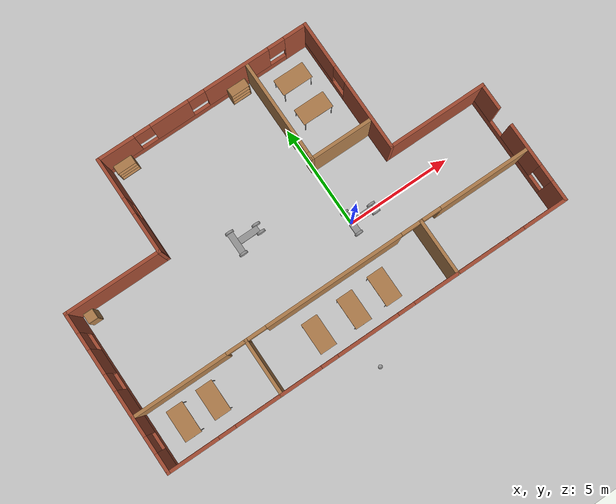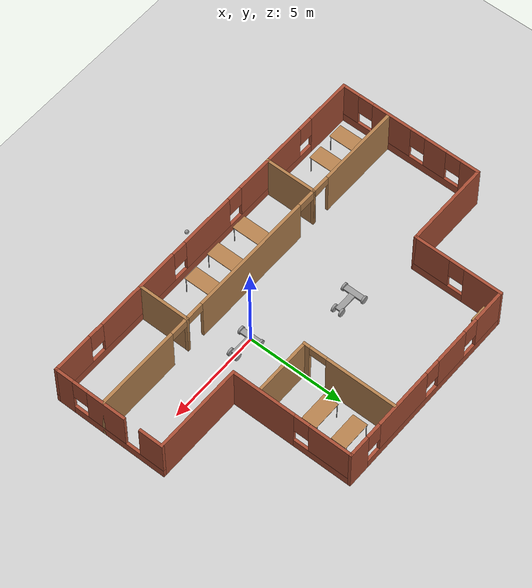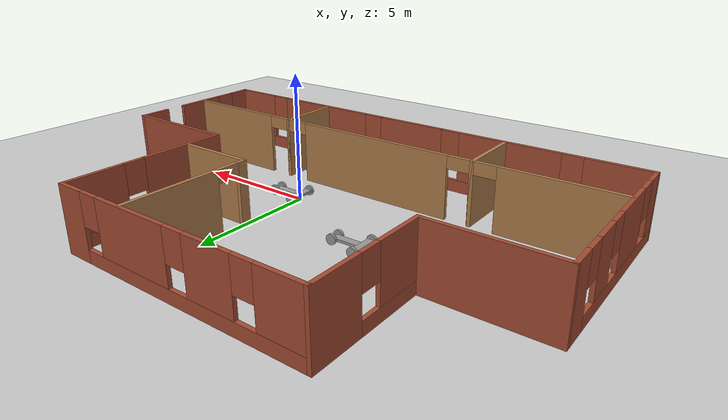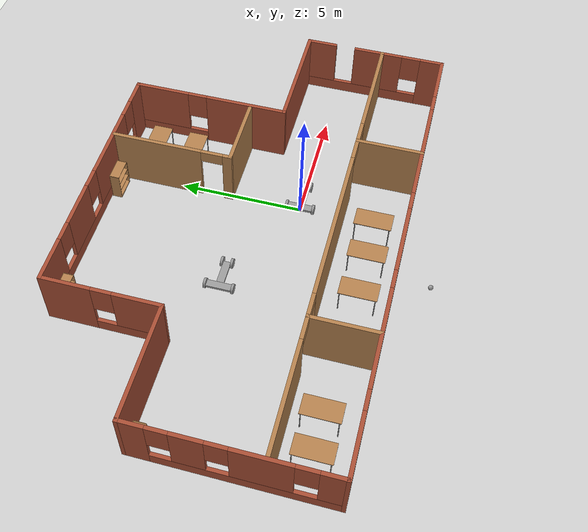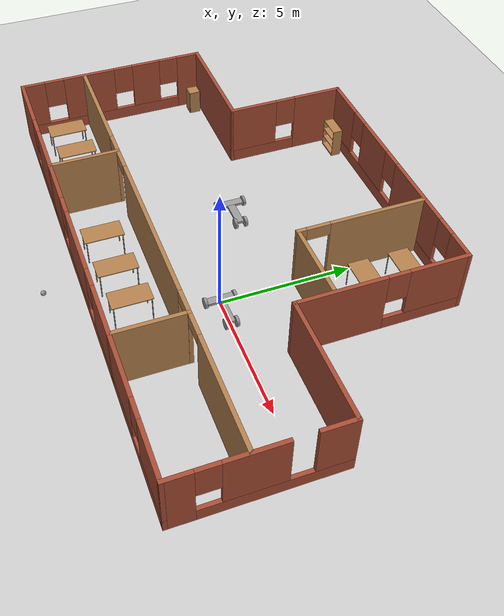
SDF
<sdf version="1.7">
 <world name="default">
  <light name="sun" type="directional">
   <pose>0 0 10 0 -0 0</pose>
   <diffuse>0.8 0.8 0.8 1</diffuse>
   <specular>0.2 0.2 0.2 1</specular>
   <attenuation>
    <range>1000</range>
    <constant>0.9</constant>
    <linear>0.01</linear>
    <quadratic>0.001</quadratic>
   </attenuation>
   <direction>-0.5 0.1 -0.9</direction>
   <spot><inner_angle>0</inner_angle><outer_angle>0</outer_angle><falloff>0</falloff></spot>
  </light>
  <model name="ground_plane">
   <static>1</static>
   <link name="link">
    <collision name="collision">
     <geometry><plane><normal>0 0 1</normal><size>100 100</size></plane></geometry>
     <surface>
      <contact><collide_bitmask>65535</collide_bitmask></contact>
      <friction><ode><mu>100</mu><mu2>50</mu2></ode></friction>
     </surface>
    </collision>
    <visual name="visual">
     <cast_shadows>0</cast_shadows>
     <geometry><plane><normal>0 0 1</normal><size>100 100</size></plane></geometry>
     <material>
      <script><uri>file://media/materials/scripts/gazebo.material</uri><name>Gazebo/Grey</name></script>
     </material>
    </visual>
   </link>
  </model>
  <gravity>0 0 -9.8</gravity>
  <magnetic_field>6e-06 2.3e-05 -4.2e-05</magnetic_field>
  <atmosphere type="adiabatic"/>
  <physics type="ode">
   <max_step_size>0.001</max_step_size>
   <real_time_factor>1</real_time_factor>
   <real_time_update_rate>1000</real_time_update_rate>
  </physics>
  <scene><ambient>0.4 0.4 0.4 1</ambient><background>0.7 0.7 0.7 1</background><shadows>1</shadows></scene>
  <spherical_coordinates>
   <surface_model>EARTH_WGS84</surface_model>
   <latitude_deg>0</latitude_deg>
   <longitude_deg>0</longitude_deg>
   <elevation>0</elevation>
   <heading_deg>0</heading_deg>
  </spherical_coordinates>
  <model name="robot">
   <link name="link_0">
    <inertial>
     <mass>1</mass>
     <inertia>
      <ixx>0.166667</ixx>
      <ixy>0</ixy>
      <ixz>0</ixz>
      <iyy>0.166667</iyy>
      <iyz>0</iyz>
      <izz>0.166667</izz>
     </inertia>
    </inertial>
    <pose>-0.408333 0 0 0 -0 0</pose>
    <visual name="visual">
     <geometry><box><size>0.3 1 0.1</size></box></geometry>
     <material>
      <lighting>1</lighting>
      <script><uri>file://media/materials/scripts/gazebo.material</uri><name>Gazebo/Grey</name></script>
      <shader type="pixel"><normal_map>__default__</normal_map></shader>
      <ambient>0.3 0.3 0.3 1</ambient>
      <diffuse>0.7 0.7 0.7 1</diffuse>
      <specular>0.01 0.01 0.01 1</specular>
      <emissive>0 0 0 1</emissive>
     </material>
    </visual>
    <collision name="collision">
     <geometry><box><size>0.3 1 0.1</size></box></geometry>
     <surface>
      <friction>
       <ode><mu>1</mu><mu2>1</mu2><fdir1>0 0 0</fdir1><slip1>0</slip1><slip2>0</slip2></ode>
       <torsional>
        <coefficient>1</coefficient>
        <patch_radius>0</patch_radius>
        <surface_radius>0</surface_radius>
        <use_patch_radius>1</use_patch_radius>
        <ode><slip>0</slip></ode>
       </torsional>
      </friction>
      <bounce><restitution_coefficient>0</restitution_coefficient><threshold>1e+06</threshold></bounce>
      <contact>
       <collide_without_contact>0</collide_without_contact>
       <collide_without_contact_bitmask>1</collide_without_contact_bitmask>
       <collide_bitmask>1</collide_bitmask>
       <ode>
        <soft_cfm>0</soft_cfm>
        <soft_erp>0.2</soft_erp>
        <kp>1e+13</kp>
        <kd>1</kd>
        <max_vel>0.01</max_vel>
        <min_depth>0</min_depth>
       </ode>
       <bullet>
        <split_impulse>1</split_impulse>
        <split_impulse_penetration_threshold>-0.01</split_impulse_penetration_threshold>
        <soft_cfm>0</soft_cfm>
        <soft_erp>0.2</soft_erp>
        <kp>1e+13</kp>
        <kd>1</kd>
       </bullet>
      </contact>
     </surface>
    </collision>
   </link>
   <link name="link_1">
    <inertial>
     <mass>1</mass>
     <inertia><ixx>0.145833</ixx><ixy>0</ixy><ixz>0</ixz><iyy>0.145833</iyy><iyz>0</iyz><izz>0.125</izz></inertia>
    </inertial>
    <pose>-0.408333 -0.550019 0 1.5707 -0 0</pose>
    <visual name="visual">
     <geometry><cylinder><radius>0.2</radius><length>0.1</length></cylinder></geometry>
     <material>
      <lighting>1</lighting>
      <script><uri>file://media/materials/scripts/gazebo.material</uri><name>Gazebo/Grey</name></script>
      <shader type="pixel"><normal_map>__default__</normal_map></shader>
      <ambient>0.3 0.3 0.3 1</ambient>
      <diffuse>0.7 0.7 0.7 1</diffuse>
      <specular>0.01 0.01 0.01 1</specular>
      <emissive>0 0 0 1</emissive>
     </material>
    </visual>
    <collision name="collision">
     <geometry><cylinder><radius>0.2</radius><length>0.1</length></cylinder></geometry>
     <surface>
      <friction>
       <ode><mu>1</mu><mu2>1</mu2><fdir1>0 0 0</fdir1><slip1>0</slip1><slip2>0</slip2></ode>
       <torsional>
        <coefficient>1</coefficient>
        <patch_radius>0</patch_radius>
        <surface_radius>0</surface_radius>
        <use_patch_radius>1</use_patch_radius>
        <ode><slip>0</slip></ode>
       </torsional>
      </friction>
      <bounce><restitution_coefficient>0</restitution_coefficient><threshold>1e+06</threshold></bounce>
      <contact>
       <collide_without_contact>0</collide_without_contact>
       <collide_without_contact_bitmask>1</collide_without_contact_bitmask>
       <collide_bitmask>1</collide_bitmask>
       <ode>
        <soft_cfm>0</soft_cfm>
        <soft_erp>0.2</soft_erp>
        <kp>1e+13</kp>
        <kd>1</kd>
        <max_vel>0.01</max_vel>
        <min_depth>0</min_depth>
       </ode>
       <bullet>
        <split_impulse>1</split_impulse>
        <split_impulse_penetration_threshold>-0.01</split_impulse_penetration_threshold>
        <soft_cfm>0</soft_cfm>
        <soft_erp>0.2</soft_erp>
        <kp>1e+13</kp>
        <kd>1</kd>
       </bullet>
      </contact>
     </surface>
    </collision>
   </link>
   <link name="link_1_clone">
    <inertial>
     <mass>1</mass>
     <inertia><ixx>0.145833</ixx><ixy>0</ixy><ixz>0</ixz><iyy>0.145833</iyy><iyz>0</iyz><izz>0.125</izz></inertia>
    </inertial>
    <pose>-0.408333 0.550019 0 1.5707 -0 0</pose>
    <visual name="visual">
     <geometry><cylinder><radius>0.2</radius><length>0.1</length></cylinder></geometry>
     <material>
      <lighting>1</lighting>
      <script><uri>file://media/materials/scripts/gazebo.material</uri><name>Gazebo/Grey</name></script>
      <shader type="pixel"><normal_map>__default__</normal_map></shader>
      <ambient>0.3 0.3 0.3 1</ambient>
      <diffuse>0.7 0.7 0.7 1</diffuse>
      <specular>0.01 0.01 0.01 1</specular>
      <emissive>0 0 0 1</emissive>
     </material>
    </visual>
    <collision name="collision">
     <geometry><cylinder><radius>0.2</radius><length>0.1</length></cylinder></geometry>
     <surface>
      <friction>
       <ode><mu>1</mu><mu2>1</mu2><fdir1>0 0 0</fdir1><slip1>0</slip1><slip2>0</slip2></ode>
       <torsional>
        <coefficient>1</coefficient>
        <patch_radius>0</patch_radius>
        <surface_radius>0</surface_radius>
        <use_patch_radius>1</use_patch_radius>
        <ode><slip>0</slip></ode>
       </torsional>
      </friction>
      <bounce><restitution_coefficient>0</restitution_coefficient><threshold>1e+06</threshold></bounce>
      <contact>
       <collide_without_contact>0</collide_without_contact>
       <collide_without_contact_bitmask>1</collide_without_contact_bitmask>
       <collide_bitmask>1</collide_bitmask>
       <ode>
        <soft_cfm>0</soft_cfm>
        <soft_erp>0.2</soft_erp>
        <kp>1e+13</kp>
        <kd>1</kd>
        <max_vel>0.01</max_vel>
        <min_depth>0</min_depth>
       </ode>
       <bullet>
        <split_impulse>1</split_impulse>
        <split_impulse_penetration_threshold>-0.01</split_impulse_penetration_threshold>
        <soft_cfm>0</soft_cfm>
        <soft_erp>0.2</soft_erp>
        <kp>1e+13</kp>
        <kd>1</kd>
       </bullet>
      </contact>
     </surface>
    </collision>
   </link>
   <link name="link_1_clone_0">
    <inertial>
     <mass>1</mass>
     <inertia><ixx>0.145833</ixx><ixy>0</ixy><ixz>0</ixz><iyy>0.145833</iyy><iyz>0</iyz><izz>0.125</izz></inertia>
    </inertial>
    <pose>0.741667 -0.200019 0 1.5707 -0 0</pose>
    <visual name="visual">
     <geometry><cylinder><radius>0.2</radius><length>0.1</length></cylinder></geometry>
     <material>
      <lighting>1</lighting>
      <script><uri>file://media/materials/scripts/gazebo.material</uri><name>Gazebo/Grey</name></script>
      <shader type="pixel"><normal_map>__default__</normal_map></shader>
      <ambient>0.3 0.3 0.3 1</ambient>
      <diffuse>0.7 0.7 0.7 1</diffuse>
      <specular>0.01 0.01 0.01 1</specular>
      <emissive>0 0 0 1</emissive>
     </material>
    </visual>
    <collision name="collision">
     <geometry><cylinder><radius>0.2</radius><length>0.1</length></cylinder></geometry>
     <surface>
      <friction>
       <ode><mu>1</mu><mu2>1</mu2><fdir1>0 0 0</fdir1><slip1>0</slip1><slip2>0</slip2></ode>
       <torsional>
        <coefficient>1</coefficient>
        <patch_radius>0</patch_radius>
        <surface_radius>0</surface_radius>
        <use_patch_radius>1</use_patch_radius>
        <ode><slip>0</slip></ode>
       </torsional>
      </friction>
      <bounce><restitution_coefficient>0</restitution_coefficient><threshold>1e+06</threshold></bounce>
      <contact>
       <collide_without_contact>0</collide_without_contact>
       <collide_without_contact_bitmask>1</collide_without_contact_bitmask>
       <collide_bitmask>1</collide_bitmask>
       <ode>
        <soft_cfm>0</soft_cfm>
        <soft_erp>0.2</soft_erp>
        <kp>1e+13</kp>
        <kd>1</kd>
        <max_vel>0.01</max_vel>
        <min_depth>0</min_depth>
       </ode>
       <bullet>
        <split_impulse>1</split_impulse>
        <split_impulse_penetration_threshold>-0.01</split_impulse_penetration_threshold>
        <soft_cfm>0</soft_cfm>
        <soft_erp>0.2</soft_erp>
        <kp>1e+13</kp>
        <kd>1</kd>
       </bullet>
      </contact>
     </surface>
    </collision>
   </link>
   <link name="link_1_clone_0_clone">
    <inertial>
     <mass>1</mass>
     <inertia><ixx>0.145833</ixx><ixy>0</ixy><ixz>0</ixz><iyy>0.145833</iyy><iyz>0</iyz><izz>0.125</izz></inertia>
    </inertial>
    <pose>0.741667 0.200019 0 1.5707 -0 0</pose>
    <visual name="visual">
     <geometry><cylinder><radius>0.2</radius><length>0.1</length></cylinder></geometry>
     <material>
      <lighting>1</lighting>
      <script><uri>file://media/materials/scripts/gazebo.material</uri><name>Gazebo/Grey</name></script>
      <shader type="pixel"><normal_map>__default__</normal_map></shader>
      <ambient>0.3 0.3 0.3 1</ambient>
      <diffuse>0.7 0.7 0.7 1</diffuse>
      <specular>0.01 0.01 0.01 1</specular>
      <emissive>0 0 0 1</emissive>
     </material>
    </visual>
    <collision name="collision">
     <geometry><cylinder><radius>0.2</radius><length>0.1</length></cylinder></geometry>
     <surface>
      <friction>
       <ode><mu>1</mu><mu2>1</mu2><fdir1>0 0 0</fdir1><slip1>0</slip1><slip2>0</slip2></ode>
       <torsional>
        <coefficient>1</coefficient>
        <patch_radius>0</patch_radius>
        <surface_radius>0</surface_radius>
        <use_patch_radius>1</use_patch_radius>
        <ode><slip>0</slip></ode>
       </torsional>
      </friction>
      <bounce><restitution_coefficient>0</restitution_coefficient><threshold>1e+06</threshold></bounce>
      <contact>
       <collide_without_contact>0</collide_without_contact>
       <collide_without_contact_bitmask>1</collide_without_contact_bitmask>
       <collide_bitmask>1</collide_bitmask>
       <ode>
        <soft_cfm>0</soft_cfm>
        <soft_erp>0.2</soft_erp>
        <kp>1e+13</kp>
        <kd>1</kd>
        <max_vel>0.01</max_vel>
        <min_depth>0</min_depth>
       </ode>
       <bullet>
        <split_impulse>1</split_impulse>
        <split_impulse_penetration_threshold>-0.01</split_impulse_penetration_threshold>
        <soft_cfm>0</soft_cfm>
        <soft_erp>0.2</soft_erp>
        <kp>1e+13</kp>
        <kd>1</kd>
       </bullet>
      </contact>
     </surface>
    </collision>
   </link>
   <link name="link_3">
    <inertial>
     <mass>1</mass>
     <inertia>
      <ixx>0.166667</ixx>
      <ixy>0</ixy>
      <ixz>0</ixz>
      <iyy>0.166667</iyy>
      <iyz>0</iyz>
      <izz>0.166667</izz>
     </inertia>
    </inertial>
    <pose>0.241667 0 0 0 -0 0</pose>
    <visual name="visual">
     <geometry><box><size>1 0.3 0.1</size></box></geometry>
     <material>
      <lighting>1</lighting>
      <script><uri>file://media/materials/scripts/gazebo.material</uri><name>Gazebo/Grey</name></script>
      <shader type="pixel"><normal_map>__default__</normal_map></shader>
      <ambient>0.3 0.3 0.3 1</ambient>
      <diffuse>0.7 0.7 0.7 1</diffuse>
      <specular>0.01 0.01 0.01 1</specular>
      <emissive>0 0 0 1</emissive>
     </material>
    </visual>
    <collision name="collision">
     <geometry><box><size>1 0.3 0.1</size></box></geometry>
     <surface>
      <friction>
       <ode><mu>1</mu><mu2>1</mu2><fdir1>0 0 0</fdir1><slip1>0</slip1><slip2>0</slip2></ode>
       <torsional>
        <coefficient>1</coefficient>
        <patch_radius>0</patch_radius>
        <surface_radius>0</surface_radius>
        <use_patch_radius>1</use_patch_radius>
        <ode><slip>0</slip></ode>
       </torsional>
      </friction>
      <bounce><restitution_coefficient>0</restitution_coefficient><threshold>1e+06</threshold></bounce>
      <contact>
       <collide_without_contact>0</collide_without_contact>
       <collide_without_contact_bitmask>1</collide_without_contact_bitmask>
       <collide_bitmask>1</collide_bitmask>
       <ode>
        <soft_cfm>0</soft_cfm>
        <soft_erp>0.2</soft_erp>
        <kp>1e+13</kp>
        <kd>1</kd>
        <max_vel>0.01</max_vel>
        <min_depth>0</min_depth>
       </ode>
       <bullet>
        <split_impulse>1</split_impulse>
        <split_impulse_penetration_threshold>-0.01</split_impulse_penetration_threshold>
        <soft_cfm>0</soft_cfm>
        <soft_erp>0.2</soft_erp>
        <kp>1e+13</kp>
        <kd>1</kd>
       </bullet>
      </contact>
     </surface>
    </collision>
   </link>
   <joint name="link_0_JOINT_0" type="revolute">
    <parent>link_0</parent>
    <child>link_1</child>
    <axis>
     <xyz>0 0 1</xyz>
     <limit>
      <lower>-1.79769e+308</lower>
      <upper>1.79769e+308</upper>
      <effort>-1</effort>
      <velocity>-1</velocity>
     </limit>
     <dynamics>
      <spring_reference>0</spring_reference>
      <spring_stiffness>0</spring_stiffness>
      <damping>0</damping>
     </dynamics>
    </axis>
    <physics>
     <ode><limit><cfm>0</cfm><erp>0.2</erp></limit><suspension><cfm>0</cfm><erp>0.2</erp></suspension></ode>
    </physics>
   </joint>
   <joint name="link_0_JOINT_1" type="revolute">
    <parent>link_0</parent>
    <child>link_1_clone</child>
    <axis>
     <xyz>0 0 1</xyz>
     <limit>
      <lower>-1.79769e+308</lower>
      <upper>1.79769e+308</upper>
      <effort>-1</effort>
      <velocity>-1</velocity>
     </limit>
     <dynamics>
      <spring_reference>0</spring_reference>
      <spring_stiffness>0</spring_stiffness>
      <damping>0</damping>
     </dynamics>
    </axis>
    <physics>
     <ode><limit><cfm>0</cfm><erp>0.2</erp></limit><suspension><cfm>0</cfm><erp>0.2</erp></suspension></ode>
    </physics>
   </joint>
   <joint name="link_0_JOINT_3" type="fixed">
    <parent>link_0</parent>
    <child>link_3</child>
    <physics>
     <ode><limit><cfm>0</cfm><erp>0.2</erp></limit><suspension><cfm>0</cfm><erp>0.2</erp></suspension></ode>
    </physics>
   </joint>
   <joint name="link_3_JOINT_5" type="revolute">
    <parent>link_3</parent>
    <child>link_1_clone_0</child>
    <axis>
     <xyz>0 0 1</xyz>
     <limit>
      <lower>-1.79769e+308</lower>
      <upper>1.79769e+308</upper>
      <effort>-1</effort>
      <velocity>-1</velocity>
     </limit>
     <dynamics>
      <spring_reference>0</spring_reference>
      <spring_stiffness>0</spring_stiffness>
      <damping>0</damping>
     </dynamics>
    </axis>
    <physics>
     <ode><limit><cfm>0</cfm><erp>0.2</erp></limit><suspension><cfm>0</cfm><erp>0.2</erp></suspension></ode>
    </physics>
   </joint>
   <joint name="link_3_JOINT_6" type="revolute">
    <parent>link_3</parent>
    <child>link_1_clone_0_clone</child>
    <axis>
     <xyz>0 0 1</xyz>
     <limit>
      <lower>-1.79769e+308</lower>
      <upper>1.79769e+308</upper>
      <effort>-1</effort>
      <velocity>-1</velocity>
     </limit>
     <dynamics>
      <spring_reference>0</spring_reference>
      <spring_stiffness>0</spring_stiffness>
      <damping>0</damping>
     </dynamics>
    </axis>
    <physics>
     <ode><limit><cfm>0</cfm><erp>0.2</erp></limit><suspension><cfm>0</cfm><erp>0.2</erp></suspension></ode>
    </physics>
   </joint>
   <static>0</static>
   <pose>0.409146 0.001566 0.200003 5e-06 -1e-06 0.004136</pose>
  </model>
  <model name="building">
   <pose>-2.195 1.715 0 0 -0 0</pose>
   <link name="Wall_10">
    <pose>-5.2249 3.79999 0 0 -0 -1.57084</pose>
    <visual name="Wall_10_Visual_0">
     <pose>-1.37612 0 1.25 0 -0 0</pose>
     <geometry><box><size>1.99776 0.15 2.5</size></box></geometry>
     <material>
      <script><uri>file://media/materials/scripts/gazebo.material</uri><name>Gazebo/Bricks</name></script>
      <ambient>1 1 1 1</ambient>
     </material>
     <meta><layer>0</layer></meta>
    </visual>
    <collision name="Wall_10_Collision_0">
     <geometry><box><size>1.99776 0.15 2.5</size></box></geometry>
     <pose>-1.37612 0 1.25 0 -0 0</pose>
    </collision>
    <visual name="Wall_10_Visual_1">
     <pose>0.998879 0 0.25 0 -0 0</pose>
     <geometry><box><size>2.75224 0.15 0.5</size></box></geometry>
     <material>
      <script><uri>file://media/materials/scripts/gazebo.material</uri><name>Gazebo/Bricks</name></script>
      <ambient>1 1 1 1</ambient>
     </material>
     <meta><layer>0</layer></meta>
    </visual>
    <collision name="Wall_10_Collision_1">
     <geometry><box><size>2.75224 0.15 0.5</size></box></geometry>
     <pose>0.998879 0 0.25 0 -0 0</pose>
    </collision>
    <visual name="Wall_10_Visual_2">
     <pose>1.39888 0 1.5 0 -0 0</pose>
     <geometry><box><size>1.95224 0.15 2</size></box></geometry>
     <material>
      <script><uri>file://media/materials/scripts/gazebo.material</uri><name>Gazebo/Bricks</name></script>
      <ambient>1 1 1 1</ambient>
     </material>
     <meta><layer>0</layer></meta>
    </visual>
    <collision name="Wall_10_Collision_2">
     <geometry><box><size>1.95224 0.15 2</size></box></geometry>
     <pose>1.39888 0 1.5 0 -0 0</pose>
    </collision>
    <visual name="Wall_10_Visual_3">
     <pose>0.022759 0 1.9 0 -0 0</pose>
     <geometry><box><size>0.8 0.15 1.2</size></box></geometry>
     <material>
      <script><uri>file://media/materials/scripts/gazebo.material</uri><name>Gazebo/Bricks</name></script>
      <ambient>1 1 1 1</ambient>
     </material>
     <meta><layer>0</layer></meta>
    </visual>
    <collision name="Wall_10_Collision_3">
     <geometry><box><size>0.8 0.15 1.2</size></box></geometry>
     <pose>0.022759 0 1.9 0 -0 0</pose>
    </collision>
   </link>
   <link name="Wall_11">
    <collision name="Wall_11_Collision">
     <geometry><box><size>4.65 0.15 2.5</size></box></geometry>
     <pose>0 0 1.25 0 -0 0</pose>
    </collision>
    <visual name="Wall_11_Visual">
     <pose>0 0 1.25 0 -0 0</pose>
     <geometry><box><size>4.65 0.15 2.5</size></box></geometry>
     <material>
      <script><uri>file://media/materials/scripts/gazebo.material</uri><name>Gazebo/Bricks</name></script>
      <ambient>1 1 1 1</ambient>
     </material>
     <meta><layer>0</layer></meta>
    </visual>
    <pose>-7.475 1.5 0 0 -0 3.14159</pose>
   </link>
   <link name="Wall_14">
    <pose>-9.725 -2.3 0 0 -0 -1.5708</pose>
    <visual name="Wall_14_Visual_0">
     <pose>-3.36591 0 1.25 0 -0 0</pose>
     <geometry><box><size>1.01819 0.15 2.5</size></box></geometry>
     <material>
      <script><uri>file://media/materials/scripts/gazebo.material</uri><name>Gazebo/Bricks</name></script>
      <ambient>1 1 1 1</ambient>
     </material>
     <meta><layer>0</layer></meta>
    </visual>
    <collision name="Wall_14_Collision_0">
     <geometry><box><size>1.01819 0.15 2.5</size></box></geometry>
     <pose>-3.36591 0 1.25 0 -0 0</pose>
    </collision>
    <visual name="Wall_14_Visual_1">
     <pose>0.509094 0 0.25 0 -0 0</pose>
     <geometry><box><size>6.73181 0.15 0.5</size></box></geometry>
     <material>
      <script><uri>file://media/materials/scripts/gazebo.material</uri><name>Gazebo/Bricks</name></script>
      <ambient>1 1 1 1</ambient>
     </material>
     <meta><layer>0</layer></meta>
    </visual>
    <collision name="Wall_14_Collision_1">
     <geometry><box><size>6.73181 0.15 0.5</size></box></geometry>
     <pose>0.509094 0 0.25 0 -0 0</pose>
    </collision>
    <visual name="Wall_14_Visual_2">
     <pose>-1.46334 0 1.5 0 -0 0</pose>
     <geometry><box><size>1.18694 0.15 2</size></box></geometry>
     <material>
      <script><uri>file://media/materials/scripts/gazebo.material</uri><name>Gazebo/Bricks</name></script>
      <ambient>1 1 1 1</ambient>
     </material>
     <meta><layer>0</layer></meta>
    </visual>
    <collision name="Wall_14_Collision_2">
     <geometry><box><size>1.18694 0.15 2</size></box></geometry>
     <pose>-1.46334 0 1.5 0 -0 0</pose>
    </collision>
    <visual name="Wall_14_Visual_3">
     <pose>1.01247 0 1.5 0 -0 0</pose>
     <geometry><box><size>2.16467 0.15 2</size></box></geometry>
     <material>
      <script><uri>file://media/materials/scripts/gazebo.material</uri><name>Gazebo/Bricks</name></script>
      <ambient>1 1 1 1</ambient>
     </material>
     <meta><layer>0</layer></meta>
    </visual>
    <collision name="Wall_14_Collision_3">
     <geometry><box><size>2.16467 0.15 2</size></box></geometry>
     <pose>1.01247 0 1.5 0 -0 0</pose>
    </collision>
    <visual name="Wall_14_Visual_4">
     <pose>3.3849 0 1.5 0 -0 0</pose>
     <geometry><box><size>0.980194 0.15 2</size></box></geometry>
     <material>
      <script><uri>file://media/materials/scripts/gazebo.material</uri><name>Gazebo/Bricks</name></script>
      <ambient>1 1 1 1</ambient>
     </material>
     <meta><layer>0</layer></meta>
    </visual>
    <collision name="Wall_14_Collision_4">
     <geometry><box><size>0.980194 0.15 2</size></box></geometry>
     <pose>3.3849 0 1.5 0 -0 0</pose>
    </collision>
    <visual name="Wall_14_Visual_5">
     <pose>-2.45681 0 1.9 0 -0 0</pose>
     <geometry><box><size>0.8 0.15 1.2</size></box></geometry>
     <material>
      <script><uri>file://media/materials/scripts/gazebo.material</uri><name>Gazebo/Bricks</name></script>
      <ambient>1 1 1 1</ambient>
     </material>
     <meta><layer>0</layer></meta>
    </visual>
    <collision name="Wall_14_Collision_5">
     <geometry><box><size>0.8 0.15 1.2</size></box></geometry>
     <pose>-2.45681 0 1.9 0 -0 0</pose>
    </collision>
    <visual name="Wall_14_Visual_6">
     <pose>-0.469869 0 1.9 0 -0 0</pose>
     <geometry><box><size>0.8 0.15 1.2</size></box></geometry>
     <material>
      <script><uri>file://media/materials/scripts/gazebo.material</uri><name>Gazebo/Bricks</name></script>
      <ambient>1 1 1 1</ambient>
     </material>
     <meta><layer>0</layer></meta>
    </visual>
    <collision name="Wall_14_Collision_6">
     <geometry><box><size>0.8 0.15 1.2</size></box></geometry>
     <pose>-0.469869 0 1.9 0 -0 0</pose>
    </collision>
    <visual name="Wall_14_Visual_7">
     <pose>2.49481 0 1.9 0 -0 0</pose>
     <geometry><box><size>0.8 0.15 1.2</size></box></geometry>
     <material>
      <script><uri>file://media/materials/scripts/gazebo.material</uri><name>Gazebo/Bricks</name></script>
      <ambient>1 1 1 1</ambient>
     </material>
     <meta><layer>0</layer></meta>
    </visual>
    <collision name="Wall_14_Collision_7">
     <geometry><box><size>0.8 0.15 1.2</size></box></geometry>
     <pose>2.49481 0 1.9 0 -0 0</pose>
    </collision>
   </link>
   <link name="Wall_17">
    <pose>-0 -6.1 0 0 -0 0</pose>
    <visual name="Wall_17_Visual_0">
     <pose>-8.55799 0 1.25 0 -0 0</pose>
     <geometry><box><size>2.48423 0.15 2.5</size></box></geometry>
     <material>
      <script><uri>file://media/materials/scripts/gazebo.material</uri><name>Gazebo/Bricks</name></script>
      <ambient>1 1 1 1</ambient>
     </material>
     <meta><layer>0</layer></meta>
    </visual>
    <collision name="Wall_17_Collision_0">
     <geometry><box><size>2.48423 0.15 2.5</size></box></geometry>
     <pose>-8.55799 0 1.25 0 -0 0</pose>
    </collision>
    <visual name="Wall_17_Visual_1">
     <pose>1.24211 0 0.25 0 -0 0</pose>
     <geometry><box><size>17.116 0.15 0.5</size></box></geometry>
     <material>
      <script><uri>file://media/materials/scripts/gazebo.material</uri><name>Gazebo/Bricks</name></script>
      <ambient>1 1 1 1</ambient>
     </material>
     <meta><layer>0</layer></meta>
    </visual>
    <collision name="Wall_17_Collision_1">
     <geometry><box><size>17.116 0.15 0.5</size></box></geometry>
     <pose>1.24211 0 0.25 0 -0 0</pose>
    </collision>
    <visual name="Wall_17_Visual_2">
     <pose>-4.44756 0 1.5 0 -0 0</pose>
     <geometry><box><size>4.13663 0.15 2</size></box></geometry>
     <material>
      <script><uri>file://media/materials/scripts/gazebo.material</uri><name>Gazebo/Bricks</name></script>
      <ambient>1 1 1 1</ambient>
     </material>
     <meta><layer>0</layer></meta>
    </visual>
    <collision name="Wall_17_Collision_2">
     <geometry><box><size>4.13663 0.15 2</size></box></geometry>
     <pose>-4.44756 0 1.5 0 -0 0</pose>
    </collision>
    <visual name="Wall_17_Visual_3">
     <pose>-0.102295 0 1.5 0 -0 0</pose>
     <geometry><box><size>2.9539 0.15 2</size></box></geometry>
     <material>
      <script><uri>file://media/materials/scripts/gazebo.material</uri><name>Gazebo/Bricks</name></script>
      <ambient>1 1 1 1</ambient>
     </material>
     <meta><layer>0</layer></meta>
    </visual>
    <collision name="Wall_17_Collision_3">
     <geometry><box><size>2.9539 0.15 2</size></box></geometry>
     <pose>-0.102295 0 1.5 0 -0 0</pose>
    </collision>
    <visual name="Wall_17_Visual_4">
     <pose>4.50009 0 1.5 0 -0 0</pose>
     <geometry><box><size>4.65087 0.15 2</size></box></geometry>
     <material>
      <script><uri>file://media/materials/scripts/gazebo.material</uri><name>Gazebo/Bricks</name></script>
      <ambient>1 1 1 1</ambient>
     </material>
     <meta><layer>0</layer></meta>
    </visual>
    <collision name="Wall_17_Collision_4">
     <geometry><box><size>4.65087 0.15 2</size></box></geometry>
     <pose>4.50009 0 1.5 0 -0 0</pose>
    </collision>
    <visual name="Wall_17_Visual_5">
     <pose>8.71281 0 1.5 0 -0 0</pose>
     <geometry><box><size>2.17458 0.15 2</size></box></geometry>
     <material>
      <script><uri>file://media/materials/scripts/gazebo.material</uri><name>Gazebo/Bricks</name></script>
      <ambient>1 1 1 1</ambient>
     </material>
     <meta><layer>0</layer></meta>
    </visual>
    <collision name="Wall_17_Collision_5">
     <geometry><box><size>2.17458 0.15 2</size></box></geometry>
     <pose>8.71281 0 1.5 0 -0 0</pose>
    </collision>
    <visual name="Wall_17_Visual_6">
     <pose>-6.91588 0 1.9 0 -0 0</pose>
     <geometry><box><size>0.8 0.15 1.2</size></box></geometry>
     <material>
      <script><uri>file://media/materials/scripts/gazebo.material</uri><name>Gazebo/Bricks</name></script>
      <ambient>1 1 1 1</ambient>
     </material>
     <meta><layer>0</layer></meta>
    </visual>
    <collision name="Wall_17_Collision_6">
     <geometry><box><size>0.8 0.15 1.2</size></box></geometry>
     <pose>-6.91588 0 1.9 0 -0 0</pose>
    </collision>
    <visual name="Wall_17_Visual_7">
     <pose>-1.97924 0 1.9 0 -0 0</pose>
     <geometry><box><size>0.8 0.15 1.2</size></box></geometry>
     <material>
      <script><uri>file://media/materials/scripts/gazebo.material</uri><name>Gazebo/Bricks</name></script>
      <ambient>1 1 1 1</ambient>
     </material>
     <meta><layer>0</layer></meta>
    </visual>
    <collision name="Wall_17_Collision_7">
     <geometry><box><size>0.8 0.15 1.2</size></box></geometry>
     <pose>-1.97924 0 1.9 0 -0 0</pose>
    </collision>
    <visual name="Wall_17_Visual_8">
     <pose>1.77465 0 1.9 0 -0 0</pose>
     <geometry><box><size>0.8 0.15 1.2</size></box></geometry>
     <material>
      <script><uri>file://media/materials/scripts/gazebo.material</uri><name>Gazebo/Bricks</name></script>
      <ambient>1 1 1 1</ambient>
     </material>
     <meta><layer>0</layer></meta>
    </visual>
    <collision name="Wall_17_Collision_8">
     <geometry><box><size>0.8 0.15 1.2</size></box></geometry>
     <pose>1.77465 0 1.9 0 -0 0</pose>
    </collision>
    <visual name="Wall_17_Visual_9">
     <pose>7.22552 0 1.9 0 -0 0</pose>
     <geometry><box><size>0.8 0.15 1.2</size></box></geometry>
     <material>
      <script><uri>file://media/materials/scripts/gazebo.material</uri><name>Gazebo/Bricks</name></script>
      <ambient>1 1 1 1</ambient>
     </material>
     <meta><layer>0</layer></meta>
    </visual>
    <collision name="Wall_17_Collision_9">
     <geometry><box><size>0.8 0.15 1.2</size></box></geometry>
     <pose>7.22552 0 1.9 0 -0 0</pose>
    </collision>
   </link>
   <link name="Wall_19">
    <pose>-0 -3.495 0 0 -0 0</pose>
    <visual name="Wall_19_Visual_0">
     <pose>-7.52876 0 1.25 0 -0 0</pose>
     <geometry><box><size>4.54248 0.15 2.5</size></box></geometry>
     <material>
      <script><uri>file://media/materials/scripts/gazebo.material</uri><name>Gazebo/Wood</name></script>
      <ambient>0 1 0 1</ambient>
     </material>
     <meta><layer>0</layer></meta>
    </visual>
    <collision name="Wall_19_Collision_0">
     <geometry><box><size>4.54248 0.15 2.5</size></box></geometry>
     <pose>-7.52876 0 1.25 0 -0 0</pose>
    </collision>
    <visual name="Wall_19_Visual_1">
     <pose>-4.29329 0 1.25 0 -0 0</pose>
     <geometry><box><size>0.128465 0.15 2.5</size></box></geometry>
     <material>
      <script><uri>file://media/materials/scripts/gazebo.material</uri><name>Gazebo/Wood</name></script>
      <ambient>0 1 0 1</ambient>
     </material>
     <meta><layer>0</layer></meta>
    </visual>
    <collision name="Wall_19_Collision_1">
     <geometry><box><size>0.128465 0.15 2.5</size></box></geometry>
     <pose>-4.29329 0 1.25 0 -0 0</pose>
    </collision>
    <visual name="Wall_19_Visual_2">
     <pose>0.007716 0 1.25 0 -0 0</pose>
     <geometry><box><size>6.67355 0.15 2.5</size></box></geometry>
     <material>
      <script><uri>file://media/materials/scripts/gazebo.material</uri><name>Gazebo/Wood</name></script>
      <ambient>0 1 0 1</ambient>
     </material>
     <meta><layer>0</layer></meta>
    </visual>
    <collision name="Wall_19_Collision_2">
     <geometry><box><size>6.67355 0.15 2.5</size></box></geometry>
     <pose>0.007716 0 1.25 0 -0 0</pose>
    </collision>
    <visual name="Wall_19_Visual_3">
     <pose>4.31981 0 1.25 0 -0 0</pose>
     <geometry><box><size>0.150647 0.15 2.5</size></box></geometry>
     <material>
      <script><uri>file://media/materials/scripts/gazebo.material</uri><name>Gazebo/Wood</name></script>
      <ambient>0 1 0 1</ambient>
     </material>
     <meta><layer>0</layer></meta>
    </visual>
    <collision name="Wall_19_Collision_3">
     <geometry><box><size>0.150647 0.15 2.5</size></box></geometry>
     <pose>4.31981 0 1.25 0 -0 0</pose>
    </collision>
    <visual name="Wall_19_Visual_4">
     <pose>7.54757 0 1.25 0 -0 0</pose>
     <geometry><box><size>4.50486 0.15 2.5</size></box></geometry>
     <material>
      <script><uri>file://media/materials/scripts/gazebo.material</uri><name>Gazebo/Wood</name></script>
      <ambient>0 1 0 1</ambient>
     </material>
     <meta><layer>0</layer></meta>
    </visual>
    <collision name="Wall_19_Collision_4">
     <geometry><box><size>4.50486 0.15 2.5</size></box></geometry>
     <pose>7.54757 0 1.25 0 -0 0</pose>
    </collision>
    <visual name="Wall_19_Visual_5">
     <pose>-4.80752 0 2.25 0 -0 0</pose>
     <geometry><box><size>0.9 0.15 0.5</size></box></geometry>
     <material>
      <script><uri>file://media/materials/scripts/gazebo.material</uri><name>Gazebo/Wood</name></script>
      <ambient>0 1 0 1</ambient>
     </material>
     <meta><layer>0</layer></meta>
    </visual>
    <collision name="Wall_19_Collision_5">
     <geometry><box><size>0.9 0.15 0.5</size></box></geometry>
     <pose>-4.80752 0 2.25 0 -0 0</pose>
    </collision>
    <visual name="Wall_19_Visual_6">
     <pose>-3.77906 0 2.25 0 -0 0</pose>
     <geometry><box><size>0.9 0.15 0.5</size></box></geometry>
     <material>
      <script><uri>file://media/materials/scripts/gazebo.material</uri><name>Gazebo/Wood</name></script>
      <ambient>0 1 0 1</ambient>
     </material>
     <meta><layer>0</layer></meta>
    </visual>
    <collision name="Wall_19_Collision_6">
     <geometry><box><size>0.9 0.15 0.5</size></box></geometry>
     <pose>-3.77906 0 2.25 0 -0 0</pose>
    </collision>
    <visual name="Wall_19_Visual_7">
     <pose>3.79449 0 2.25 0 -0 0</pose>
     <geometry><box><size>0.9 0.15 0.5</size></box></geometry>
     <material>
      <script><uri>file://media/materials/scripts/gazebo.material</uri><name>Gazebo/Wood</name></script>
      <ambient>0 1 0 1</ambient>
     </material>
     <meta><layer>0</layer></meta>
    </visual>
    <collision name="Wall_19_Collision_7">
     <geometry><box><size>0.9 0.15 0.5</size></box></geometry>
     <pose>3.79449 0 2.25 0 -0 0</pose>
    </collision>
    <visual name="Wall_19_Visual_8">
     <pose>4.84514 0 2.25 0 -0 0</pose>
     <geometry><box><size>0.9 0.15 0.5</size></box></geometry>
     <material>
      <script><uri>file://media/materials/scripts/gazebo.material</uri><name>Gazebo/Wood</name></script>
      <ambient>0 1 0 1</ambient>
     </material>
     <meta><layer>0</layer></meta>
    </visual>
    <collision name="Wall_19_Collision_8">
     <geometry><box><size>0.9 0.15 0.5</size></box></geometry>
     <pose>4.84514 0 2.25 0 -0 0</pose>
    </collision>
   </link>
   <link name="Wall_21">
    <collision name="Wall_21_Collision">
     <geometry><box><size>2.755 0.15 2.5</size></box></geometry>
     <pose>0 0 1.25 0 -0 0</pose>
    </collision>
    <visual name="Wall_21_Visual">
     <pose>0 0 1.25 0 -0 0</pose>
     <geometry><box><size>2.755 0.15 2.5</size></box></geometry>
     <material>
      <script><uri>file://media/materials/scripts/gazebo.material</uri><name>Gazebo/Wood</name></script>
      <ambient>1 1 1 1</ambient>
     </material>
     <meta><layer>0</layer></meta>
    </visual>
    <pose>-4.313 -4.7975 0 0 -0 -1.5708</pose>
   </link>
   <link name="Wall_23">
    <collision name="Wall_23_Collision">
     <geometry><box><size>2.755 0.15 2.5</size></box></geometry>
     <pose>0 0 1.25 0 -0 0</pose>
    </collision>
    <visual name="Wall_23_Visual">
     <pose>0 0 1.25 0 -0 0</pose>
     <geometry><box><size>2.755 0.15 2.5</size></box></geometry>
     <material>
      <script><uri>file://media/materials/scripts/gazebo.material</uri><name>Gazebo/Wood</name></script>
      <ambient>1 1 1 1</ambient>
     </material>
     <meta><layer>0</layer></meta>
    </visual>
    <pose>4.313 -4.7975 0 0 -0 -1.5708</pose>
   </link>
   <link name="Wall_27">
    <pose>2.09696 3.60453 0 0 -0 -1.5708</pose>
    <visual name="Wall_27_Visual_0">
     <pose>-0.643715 0 1.25 0 -0 0</pose>
     <geometry><box><size>3.71257 0.15 2.5</size></box></geometry>
     <material>
      <script><uri>file://media/materials/scripts/gazebo.material</uri><name>Gazebo/Wood</name></script>
      <ambient>1 1 1 1</ambient>
     </material>
     <meta><layer>0</layer></meta>
    </visual>
    <collision name="Wall_27_Collision_0">
     <geometry><box><size>3.71257 0.15 2.5</size></box></geometry>
     <pose>-0.643715 0 1.25 0 -0 0</pose>
    </collision>
    <visual name="Wall_27_Visual_1">
     <pose>2.30628 0 1.25 0 -0 0</pose>
     <geometry><box><size>0.38743 0.15 2.5</size></box></geometry>
     <material>
      <script><uri>file://media/materials/scripts/gazebo.material</uri><name>Gazebo/Wood</name></script>
      <ambient>1 1 1 1</ambient>
     </material>
     <meta><layer>0</layer></meta>
    </visual>
    <collision name="Wall_27_Collision_1">
     <geometry><box><size>0.38743 0.15 2.5</size></box></geometry>
     <pose>2.30628 0 1.25 0 -0 0</pose>
    </collision>
    <visual name="Wall_27_Visual_2">
     <pose>1.66257 0 2.25 0 -0 0</pose>
     <geometry><box><size>0.9 0.15 0.5</size></box></geometry>
     <material>
      <script><uri>file://media/materials/scripts/gazebo.material</uri><name>Gazebo/Wood</name></script>
      <ambient>1 1 1 1</ambient>
     </material>
     <meta><layer>0</layer></meta>
    </visual>
    <collision name="Wall_27_Collision_2">
     <geometry><box><size>0.9 0.15 0.5</size></box></geometry>
     <pose>1.66257 0 2.25 0 -0 0</pose>
    </collision>
   </link>
   <link name="Wall_28">
    <collision name="Wall_28_Collision">
     <geometry><box><size>3 0.15 2.5</size></box></geometry>
     <pose>0 0 1.25 0 -0 0</pose>
    </collision>
    <visual name="Wall_28_Visual">
     <pose>0 0 1.25 0 -0 0</pose>
     <geometry><box><size>3 0.15 2.5</size></box></geometry>
     <material>
      <script><uri>file://media/materials/scripts/gazebo.material</uri><name>Gazebo/Wood</name></script>
      <ambient>1 1 1 1</ambient>
     </material>
     <meta><layer>0</layer></meta>
    </visual>
    <pose>3.52196 1.17954 0 0 -0 0</pose>
   </link>
   <link name="Wall_6">
    <pose>9.725 -3.171 0 0 -0 1.5708</pose>
    <visual name="Wall_6_Visual_0">
     <pose>-2.49676 0 1.25 0 -0 0</pose>
     <geometry><box><size>1.01448 0.15 2.5</size></box></geometry>
     <material>
      <script><uri>file://media/materials/scripts/gazebo.material</uri><name>Gazebo/Bricks</name></script>
      <ambient>1 1 1 1</ambient>
     </material>
     <meta><layer>0</layer></meta>
    </visual>
    <collision name="Wall_6_Collision_0">
     <geometry><box><size>1.01448 0.15 2.5</size></box></geometry>
     <pose>-2.49676 0 1.25 0 -0 0</pose>
    </collision>
    <visual name="Wall_6_Visual_1">
     <pose>0.507238 0 0.25 0 -0 0</pose>
     <geometry><box><size>4.99352 0.15 0.5</size></box></geometry>
     <material>
      <script><uri>file://media/materials/scripts/gazebo.material</uri><name>Gazebo/Bricks</name></script>
      <ambient>1 1 1 1</ambient>
     </material>
     <meta><layer>0</layer></meta>
    </visual>
    <collision name="Wall_6_Collision_1">
     <geometry><box><size>4.99352 0.15 0.5</size></box></geometry>
     <pose>0.507238 0 0.25 0 -0 0</pose>
    </collision>
    <visual name="Wall_6_Visual_2">
     <pose>-0.143582 0 1.5 0 -0 0</pose>
     <geometry><box><size>2.09188 0.15 2</size></box></geometry>
     <material>
      <script><uri>file://media/materials/scripts/gazebo.material</uri><name>Gazebo/Bricks</name></script>
      <ambient>1 1 1 1</ambient>
     </material>
     <meta><layer>0</layer></meta>
    </visual>
    <collision name="Wall_6_Collision_2">
     <geometry><box><size>2.09188 0.15 2</size></box></geometry>
     <pose>-0.143582 0 1.5 0 -0 0</pose>
    </collision>
    <visual name="Wall_6_Visual_3">
     <pose>2.35318 0 1.5 0 -0 0</pose>
     <geometry><box><size>1.30164 0.15 2</size></box></geometry>
     <material>
      <script><uri>file://media/materials/scripts/gazebo.material</uri><name>Gazebo/Bricks</name></script>
      <ambient>1 1 1 1</ambient>
     </material>
     <meta><layer>0</layer></meta>
    </visual>
    <collision name="Wall_6_Collision_3">
     <geometry><box><size>1.30164 0.15 2</size></box></geometry>
     <pose>2.35318 0 1.5 0 -0 0</pose>
    </collision>
    <visual name="Wall_6_Visual_4">
     <pose>-1.58952 0 1.9 0 -0 0</pose>
     <geometry><box><size>0.8 0.15 1.2</size></box></geometry>
     <material>
      <script><uri>file://media/materials/scripts/gazebo.material</uri><name>Gazebo/Bricks</name></script>
      <ambient>1 1 1 1</ambient>
     </material>
     <meta><layer>0</layer></meta>
    </visual>
    <collision name="Wall_6_Collision_4">
     <geometry><box><size>0.8 0.15 1.2</size></box></geometry>
     <pose>-1.58952 0 1.9 0 -0 0</pose>
    </collision>
    <visual name="Wall_6_Visual_5">
     <pose>0.902359 0 1.9 0 -0 0</pose>
     <geometry><box><size>0 0.15 1.2</size></box></geometry>
     <material>
      <script><uri>file://media/materials/scripts/gazebo.material</uri><name>Gazebo/Bricks</name></script>
      <ambient>1 1 1 1</ambient>
     </material>
     <meta><layer>0</layer></meta>
    </visual>
    <collision name="Wall_6_Collision_5">
     <geometry><box><size>0 0.15 1.2</size></box></geometry>
     <pose>0.902359 0 1.9 0 -0 0</pose>
    </collision>
   </link>
   <link name="Wall_7">
    <collision name="Wall_7_Collision">
     <geometry><box><size>4.77281 0.15 2.5</size></box></geometry>
     <pose>0 0 1.25 0 -0 0</pose>
    </collision>
    <visual name="Wall_7_Visual">
     <pose>0 0 1.25 0 -0 0</pose>
     <geometry><box><size>4.77281 0.15 2.5</size></box></geometry>
     <material>
      <script><uri>file://media/materials/scripts/gazebo.material</uri><name>Gazebo/Bricks</name></script>
      <ambient>1 1 1 1</ambient>
     </material>
     <meta><layer>0</layer></meta>
    </visual>
    <pose>7.4135 -0.242 0 0 -0 3.14159</pose>
   </link>
   <link name="Wall_8">
    <pose>5.102 2.929 0 0 -0 1.5708</pose>
    <visual name="Wall_8_Visual_0">
     <pose>-1.54193 0 1.25 0 -0 0</pose>
     <geometry><box><size>3.40815 0.15 2.5</size></box></geometry>
     <material>
      <script><uri>file://media/materials/scripts/gazebo.material</uri><name>Gazebo/Bricks</name></script>
      <ambient>1 1 1 1</ambient>
     </material>
     <meta><layer>0</layer></meta>
    </visual>
    <collision name="Wall_8_Collision_0">
     <geometry><box><size>3.40815 0.15 2.5</size></box></geometry>
     <pose>-1.54193 0 1.25 0 -0 0</pose>
    </collision>
    <visual name="Wall_8_Visual_1">
     <pose>1.70407 0 0.25 0 -0 0</pose>
     <geometry><box><size>3.08385 0.15 0.5</size></box></geometry>
     <material>
      <script><uri>file://media/materials/scripts/gazebo.material</uri><name>Gazebo/Bricks</name></script>
      <ambient>1 1 1 1</ambient>
     </material>
     <meta><layer>0</layer></meta>
    </visual>
    <collision name="Wall_8_Collision_1">
     <geometry><box><size>3.08385 0.15 0.5</size></box></geometry>
     <pose>1.70407 0 0.25 0 -0 0</pose>
    </collision>
    <visual name="Wall_8_Visual_2">
     <pose>2.10407 0 1.5 0 -0 0</pose>
     <geometry><box><size>2.28385 0.15 2</size></box></geometry>
     <material>
      <script><uri>file://media/materials/scripts/gazebo.material</uri><name>Gazebo/Bricks</name></script>
      <ambient>1 1 1 1</ambient>
     </material>
     <meta><layer>0</layer></meta>
    </visual>
    <collision name="Wall_8_Collision_2">
     <geometry><box><size>2.28385 0.15 2</size></box></geometry>
     <pose>2.10407 0 1.5 0 -0 0</pose>
    </collision>
    <visual name="Wall_8_Visual_3">
     <pose>0.562146 0 1.9 0 -0 0</pose>
     <geometry><box><size>0.8 0.15 1.2</size></box></geometry>
     <material>
      <script><uri>file://media/materials/scripts/gazebo.material</uri><name>Gazebo/Bricks</name></script>
      <ambient>1 1 1 1</ambient>
     </material>
     <meta><layer>0</layer></meta>
    </visual>
    <collision name="Wall_8_Collision_3">
     <geometry><box><size>0.8 0.15 1.2</size></box></geometry>
     <pose>0.562146 0 1.9 0 -0 0</pose>
    </collision>
   </link>
   <link name="Wall_9">
    <pose>-0.061396 6.09999 0 0 -0 -3.14159</pose>
    <visual name="Wall_9_Visual_0">
     <pose>-4.65242 0 1.25 0 -0 0</pose>
     <geometry><box><size>1.17196 0.15 2.5</size></box></geometry>
     <material>
      <script><uri>file://media/materials/scripts/gazebo.material</uri><name>Gazebo/Bricks</name></script>
      <ambient>1 1 1 1</ambient>
     </material>
     <meta><layer>0</layer></meta>
    </visual>
    <collision name="Wall_9_Collision_0">
     <geometry><box><size>1.17196 0.15 2.5</size></box></geometry>
     <pose>-4.65242 0 1.25 0 -0 0</pose>
    </collision>
    <visual name="Wall_9_Visual_1">
     <pose>0.58598 0 0.25 0 -0 0</pose>
     <geometry><box><size>9.30483 0.15 0.5</size></box></geometry>
     <material>
      <script><uri>file://media/materials/scripts/gazebo.material</uri><name>Gazebo/Bricks</name></script>
      <ambient>1 1 1 1</ambient>
     </material>
     <meta><layer>0</layer></meta>
    </visual>
    <collision name="Wall_9_Collision_1">
     <geometry><box><size>9.30483 0.15 0.5</size></box></geometry>
     <pose>0.58598 0 0.25 0 -0 0</pose>
    </collision>
    <visual name="Wall_9_Visual_2">
     <pose>-1.66935 0 1.5 0 -0 0</pose>
     <geometry><box><size>3.19417 0.15 2</size></box></geometry>
     <material>
      <script><uri>file://media/materials/scripts/gazebo.material</uri><name>Gazebo/Bricks</name></script>
      <ambient>1 1 1 1</ambient>
     </material>
     <meta><layer>0</layer></meta>
    </visual>
    <collision name="Wall_9_Collision_2">
     <geometry><box><size>3.19417 0.15 2</size></box></geometry>
     <pose>-1.66935 0 1.5 0 -0 0</pose>
    </collision>
    <visual name="Wall_9_Visual_3">
     <pose>1.66831 0 1.5 0 -0 0</pose>
     <geometry><box><size>1.88115 0.15 2</size></box></geometry>
     <material>
      <script><uri>file://media/materials/scripts/gazebo.material</uri><name>Gazebo/Bricks</name></script>
      <ambient>1 1 1 1</ambient>
     </material>
     <meta><layer>0</layer></meta>
    </visual>
    <collision name="Wall_9_Collision_3">
     <geometry><box><size>1.88115 0.15 2</size></box></geometry>
     <pose>1.66831 0 1.5 0 -0 0</pose>
    </collision>
    <visual name="Wall_9_Visual_4">
     <pose>4.32364 0 1.5 0 -0 0</pose>
     <geometry><box><size>1.82951 0.15 2</size></box></geometry>
     <material>
      <script><uri>file://media/materials/scripts/gazebo.material</uri><name>Gazebo/Bricks</name></script>
      <ambient>1 1 1 1</ambient>
     </material>
     <meta><layer>0</layer></meta>
    </visual>
    <collision name="Wall_9_Collision_4">
     <geometry><box><size>1.82951 0.15 2</size></box></geometry>
     <pose>4.32364 0 1.5 0 -0 0</pose>
    </collision>
    <visual name="Wall_9_Visual_5">
     <pose>-3.66644 0 1.9 0 -0 0</pose>
     <geometry><box><size>0.8 0.15 1.2</size></box></geometry>
     <material>
      <script><uri>file://media/materials/scripts/gazebo.material</uri><name>Gazebo/Bricks</name></script>
      <ambient>1 1 1 1</ambient>
     </material>
     <meta><layer>0</layer></meta>
    </visual>
    <collision name="Wall_9_Collision_5">
     <geometry><box><size>0.8 0.15 1.2</size></box></geometry>
     <pose>-3.66644 0 1.9 0 -0 0</pose>
    </collision>
    <visual name="Wall_9_Visual_6">
     <pose>0.327732 0 1.9 0 -0 0</pose>
     <geometry><box><size>0.8 0.15 1.2</size></box></geometry>
     <material>
      <script><uri>file://media/materials/scripts/gazebo.material</uri><name>Gazebo/Bricks</name></script>
      <ambient>1 1 1 1</ambient>
     </material>
     <meta><layer>0</layer></meta>
    </visual>
    <collision name="Wall_9_Collision_6">
     <geometry><box><size>0.8 0.15 1.2</size></box></geometry>
     <pose>0.327732 0 1.9 0 -0 0</pose>
    </collision>
    <visual name="Wall_9_Visual_7">
     <pose>3.00888 0 1.9 0 -0 0</pose>
     <geometry><box><size>0.8 0.15 1.2</size></box></geometry>
     <material>
      <script><uri>file://media/materials/scripts/gazebo.material</uri><name>Gazebo/Bricks</name></script>
      <ambient>1 1 1 1</ambient>
     </material>
     <meta><layer>0</layer></meta>
    </visual>
    <collision name="Wall_9_Collision_7">
     <geometry><box><size>0.8 0.15 1.2</size></box></geometry>
     <pose>3.00888 0 1.9 0 -0 0</pose>
    </collision>
   </link>
   <static>1</static>
  </model>
  <model name="robot_clone">
   <link name="link_0">
    <inertial>
     <mass>1</mass>
     <inertia>
      <ixx>0.166667</ixx>
      <ixy>0</ixy>
      <ixz>0</ixz>
      <iyy>0.166667</iyy>
      <iyz>0</iyz>
      <izz>0.166667</izz>
     </inertia>
    </inertial>
    <pose>-0.408333 0 0 0 -0 0</pose>
    <visual name="visual">
     <geometry><box><size>0.3 1 0.1</size></box></geometry>
     <material>
      <lighting>1</lighting>
      <script><uri>file://media/materials/scripts/gazebo.material</uri><name>Gazebo/Grey</name></script>
      <shader type="pixel"><normal_map>__default__</normal_map></shader>
      <ambient>0.3 0.3 0.3 1</ambient>
      <diffuse>0.7 0.7 0.7 1</diffuse>
      <specular>0.01 0.01 0.01 1</specular>
      <emissive>0 0 0 1</emissive>
     </material>
    </visual>
    <collision name="collision">
     <geometry><box><size>0.3 1 0.1</size></box></geometry>
     <surface>
      <friction>
       <ode><mu>1</mu><mu2>1</mu2><fdir1>0 0 0</fdir1><slip1>0</slip1><slip2>0</slip2></ode>
       <torsional>
        <coefficient>1</coefficient>
        <patch_radius>0</patch_radius>
        <surface_radius>0</surface_radius>
        <use_patch_radius>1</use_patch_radius>
        <ode><slip>0</slip></ode>
       </torsional>
      </friction>
      <bounce><restitution_coefficient>0</restitution_coefficient><threshold>1e+06</threshold></bounce>
      <contact>
       <collide_without_contact>0</collide_without_contact>
       <collide_without_contact_bitmask>1</collide_without_contact_bitmask>
       <collide_bitmask>1</collide_bitmask>
       <ode>
        <soft_cfm>0</soft_cfm>
        <soft_erp>0.2</soft_erp>
        <kp>1e+13</kp>
        <kd>1</kd>
        <max_vel>0.01</max_vel>
        <min_depth>0</min_depth>
       </ode>
       <bullet>
        <split_impulse>1</split_impulse>
        <split_impulse_penetration_threshold>-0.01</split_impulse_penetration_threshold>
        <soft_cfm>0</soft_cfm>
        <soft_erp>0.2</soft_erp>
        <kp>1e+13</kp>
        <kd>1</kd>
       </bullet>
      </contact>
     </surface>
    </collision>
   </link>
   <link name="link_1">
    <inertial>
     <mass>1</mass>
     <inertia><ixx>0.145833</ixx><ixy>0</ixy><ixz>0</ixz><iyy>0.145833</iyy><iyz>0</iyz><izz>0.125</izz></inertia>
    </inertial>
    <pose>-0.408333 -0.550019 0 1.5707 -0 0</pose>
    <visual name="visual">
     <geometry><cylinder><radius>0.2</radius><length>0.1</length></cylinder></geometry>
     <material>
      <lighting>1</lighting>
      <script><uri>file://media/materials/scripts/gazebo.material</uri><name>Gazebo/Grey</name></script>
      <shader type="pixel"><normal_map>__default__</normal_map></shader>
      <ambient>0.3 0.3 0.3 1</ambient>
      <diffuse>0.7 0.7 0.7 1</diffuse>
      <specular>0.01 0.01 0.01 1</specular>
      <emissive>0 0 0 1</emissive>
     </material>
    </visual>
    <collision name="collision">
     <geometry><cylinder><radius>0.2</radius><length>0.1</length></cylinder></geometry>
     <surface>
      <friction>
       <ode><mu>1</mu><mu2>1</mu2><fdir1>0 0 0</fdir1><slip1>0</slip1><slip2>0</slip2></ode>
       <torsional>
        <coefficient>1</coefficient>
        <patch_radius>0</patch_radius>
        <surface_radius>0</surface_radius>
        <use_patch_radius>1</use_patch_radius>
        <ode><slip>0</slip></ode>
       </torsional>
      </friction>
      <bounce><restitution_coefficient>0</restitution_coefficient><threshold>1e+06</threshold></bounce>
      <contact>
       <collide_without_contact>0</collide_without_contact>
       <collide_without_contact_bitmask>1</collide_without_contact_bitmask>
       <collide_bitmask>1</collide_bitmask>
       <ode>
        <soft_cfm>0</soft_cfm>
        <soft_erp>0.2</soft_erp>
        <kp>1e+13</kp>
        <kd>1</kd>
        <max_vel>0.01</max_vel>
        <min_depth>0</min_depth>
       </ode>
       <bullet>
        <split_impulse>1</split_impulse>
        <split_impulse_penetration_threshold>-0.01</split_impulse_penetration_threshold>
        <soft_cfm>0</soft_cfm>
        <soft_erp>0.2</soft_erp>
        <kp>1e+13</kp>
        <kd>1</kd>
       </bullet>
      </contact>
     </surface>
    </collision>
   </link>
   <link name="link_1_clone">
    <inertial>
     <mass>1</mass>
     <inertia><ixx>0.145833</ixx><ixy>0</ixy><ixz>0</ixz><iyy>0.145833</iyy><iyz>0</iyz><izz>0.125</izz></inertia>
    </inertial>
    <pose>-0.408333 0.550019 0 1.5707 -0 0</pose>
    <visual name="visual">
     <geometry><cylinder><radius>0.2</radius><length>0.1</length></cylinder></geometry>
     <material>
      <lighting>1</lighting>
      <script><uri>file://media/materials/scripts/gazebo.material</uri><name>Gazebo/Grey</name></script>
      <shader type="pixel"><normal_map>__default__</normal_map></shader>
      <ambient>0.3 0.3 0.3 1</ambient>
      <diffuse>0.7 0.7 0.7 1</diffuse>
      <specular>0.01 0.01 0.01 1</specular>
      <emissive>0 0 0 1</emissive>
     </material>
    </visual>
    <collision name="collision">
     <geometry><cylinder><radius>0.2</radius><length>0.1</length></cylinder></geometry>
     <surface>
      <friction>
       <ode><mu>1</mu><mu2>1</mu2><fdir1>0 0 0</fdir1><slip1>0</slip1><slip2>0</slip2></ode>
       <torsional>
        <coefficient>1</coefficient>
        <patch_radius>0</patch_radius>
        <surface_radius>0</surface_radius>
        <use_patch_radius>1</use_patch_radius>
        <ode><slip>0</slip></ode>
       </torsional>
      </friction>
      <bounce><restitution_coefficient>0</restitution_coefficient><threshold>1e+06</threshold></bounce>
      <contact>
       <collide_without_contact>0</collide_without_contact>
       <collide_without_contact_bitmask>1</collide_without_contact_bitmask>
       <collide_bitmask>1</collide_bitmask>
       <ode>
        <soft_cfm>0</soft_cfm>
        <soft_erp>0.2</soft_erp>
        <kp>1e+13</kp>
        <kd>1</kd>
        <max_vel>0.01</max_vel>
        <min_depth>0</min_depth>
       </ode>
       <bullet>
        <split_impulse>1</split_impulse>
        <split_impulse_penetration_threshold>-0.01</split_impulse_penetration_threshold>
        <soft_cfm>0</soft_cfm>
        <soft_erp>0.2</soft_erp>
        <kp>1e+13</kp>
        <kd>1</kd>
       </bullet>
      </contact>
     </surface>
    </collision>
   </link>
   <link name="link_1_clone_0">
    <inertial>
     <mass>1</mass>
     <inertia><ixx>0.145833</ixx><ixy>0</ixy><ixz>0</ixz><iyy>0.145833</iyy><iyz>0</iyz><izz>0.125</izz></inertia>
    </inertial>
    <pose>0.741667 -0.200019 0 1.5707 -0 0</pose>
    <visual name="visual">
     <geometry><cylinder><radius>0.2</radius><length>0.1</length></cylinder></geometry>
     <material>
      <lighting>1</lighting>
      <script><uri>file://media/materials/scripts/gazebo.material</uri><name>Gazebo/Grey</name></script>
      <shader type="pixel"><normal_map>__default__</normal_map></shader>
      <ambient>0.3 0.3 0.3 1</ambient>
      <diffuse>0.7 0.7 0.7 1</diffuse>
      <specular>0.01 0.01 0.01 1</specular>
      <emissive>0 0 0 1</emissive>
     </material>
    </visual>
    <collision name="collision">
     <geometry><cylinder><radius>0.2</radius><length>0.1</length></cylinder></geometry>
     <surface>
      <friction>
       <ode><mu>1</mu><mu2>1</mu2><fdir1>0 0 0</fdir1><slip1>0</slip1><slip2>0</slip2></ode>
       <torsional>
        <coefficient>1</coefficient>
        <patch_radius>0</patch_radius>
        <surface_radius>0</surface_radius>
        <use_patch_radius>1</use_patch_radius>
        <ode><slip>0</slip></ode>
       </torsional>
      </friction>
      <bounce><restitution_coefficient>0</restitution_coefficient><threshold>1e+06</threshold></bounce>
      <contact>
       <collide_without_contact>0</collide_without_contact>
       <collide_without_contact_bitmask>1</collide_without_contact_bitmask>
       <collide_bitmask>1</collide_bitmask>
       <ode>
        <soft_cfm>0</soft_cfm>
        <soft_erp>0.2</soft_erp>
        <kp>1e+13</kp>
        <kd>1</kd>
        <max_vel>0.01</max_vel>
        <min_depth>0</min_depth>
       </ode>
       <bullet>
        <split_impulse>1</split_impulse>
        <split_impulse_penetration_threshold>-0.01</split_impulse_penetration_threshold>
        <soft_cfm>0</soft_cfm>
        <soft_erp>0.2</soft_erp>
        <kp>1e+13</kp>
        <kd>1</kd>
       </bullet>
      </contact>
     </surface>
    </collision>
   </link>
   <link name="link_1_clone_0_clone">
    <inertial>
     <mass>1</mass>
     <inertia><ixx>0.145833</ixx><ixy>0</ixy><ixz>0</ixz><iyy>0.145833</iyy><iyz>0</iyz><izz>0.125</izz></inertia>
    </inertial>
    <pose>0.741667 0.200019 0 1.5707 -0 0</pose>
    <visual name="visual">
     <geometry><cylinder><radius>0.2</radius><length>0.1</length></cylinder></geometry>
     <material>
      <lighting>1</lighting>
      <script><uri>file://media/materials/scripts/gazebo.material</uri><name>Gazebo/Grey</name></script>
      <shader type="pixel"><normal_map>__default__</normal_map></shader>
      <ambient>0.3 0.3 0.3 1</ambient>
      <diffuse>0.7 0.7 0.7 1</diffuse>
      <specular>0.01 0.01 0.01 1</specular>
      <emissive>0 0 0 1</emissive>
     </material>
    </visual>
    <collision name="collision">
     <geometry><cylinder><radius>0.2</radius><length>0.1</length></cylinder></geometry>
     <surface>
      <friction>
       <ode><mu>1</mu><mu2>1</mu2><fdir1>0 0 0</fdir1><slip1>0</slip1><slip2>0</slip2></ode>
       <torsional>
        <coefficient>1</coefficient>
        <patch_radius>0</patch_radius>
        <surface_radius>0</surface_radius>
        <use_patch_radius>1</use_patch_radius>
        <ode><slip>0</slip></ode>
       </torsional>
      </friction>
      <bounce><restitution_coefficient>0</restitution_coefficient><threshold>1e+06</threshold></bounce>
      <contact>
       <collide_without_contact>0</collide_without_contact>
       <collide_without_contact_bitmask>1</collide_without_contact_bitmask>
       <collide_bitmask>1</collide_bitmask>
       <ode>
        <soft_cfm>0</soft_cfm>
        <soft_erp>0.2</soft_erp>
        <kp>1e+13</kp>
        <kd>1</kd>
        <max_vel>0.01</max_vel>
        <min_depth>0</min_depth>
       </ode>
       <bullet>
        <split_impulse>1</split_impulse>
        <split_impulse_penetration_threshold>-0.01</split_impulse_penetration_threshold>
        <soft_cfm>0</soft_cfm>
        <soft_erp>0.2</soft_erp>
        <kp>1e+13</kp>
        <kd>1</kd>
       </bullet>
      </contact>
     </surface>
    </collision>
   </link>
   <link name="link_3">
    <inertial>
     <mass>1</mass>
     <inertia>
      <ixx>0.166667</ixx>
      <ixy>0</ixy>
      <ixz>0</ixz>
      <iyy>0.166667</iyy>
      <iyz>0</iyz>
      <izz>0.166667</izz>
     </inertia>
    </inertial>
    <pose>0.241667 0 0 0 -0 0</pose>
    <visual name="visual">
     <geometry><box><size>1 0.3 0.1</size></box></geometry>
     <material>
      <lighting>1</lighting>
      <script><uri>file://media/materials/scripts/gazebo.material</uri><name>Gazebo/Grey</name></script>
      <shader type="pixel"><normal_map>__default__</normal_map></shader>
      <ambient>0.3 0.3 0.3 1</ambient>
      <diffuse>0.7 0.7 0.7 1</diffuse>
      <specular>0.01 0.01 0.01 1</specular>
      <emissive>0 0 0 1</emissive>
     </material>
    </visual>
    <collision name="collision">
     <geometry><box><size>1 0.3 0.1</size></box></geometry>
     <surface>
      <friction>
       <ode><mu>1</mu><mu2>1</mu2><fdir1>0 0 0</fdir1><slip1>0</slip1><slip2>0</slip2></ode>
       <torsional>
        <coefficient>1</coefficient>
        <patch_radius>0</patch_radius>
        <surface_radius>0</surface_radius>
        <use_patch_radius>1</use_patch_radius>
        <ode><slip>0</slip></ode>
       </torsional>
      </friction>
      <bounce><restitution_coefficient>0</restitution_coefficient><threshold>1e+06</threshold></bounce>
      <contact>
       <collide_without_contact>0</collide_without_contact>
       <collide_without_contact_bitmask>1</collide_without_contact_bitmask>
       <collide_bitmask>1</collide_bitmask>
       <ode>
        <soft_cfm>0</soft_cfm>
        <soft_erp>0.2</soft_erp>
        <kp>1e+13</kp>
        <kd>1</kd>
        <max_vel>0.01</max_vel>
        <min_depth>0</min_depth>
       </ode>
       <bullet>
        <split_impulse>1</split_impulse>
        <split_impulse_penetration_threshold>-0.01</split_impulse_penetration_threshold>
        <soft_cfm>0</soft_cfm>
        <soft_erp>0.2</soft_erp>
        <kp>1e+13</kp>
        <kd>1</kd>
       </bullet>
      </contact>
     </surface>
    </collision>
   </link>
   <joint name="link_0_JOINT_0" type="revolute">
    <parent>link_0</parent>
    <child>link_1</child>
    <axis>
     <xyz>0 0 1</xyz>
     <limit>
      <lower>-1.79769e+308</lower>
      <upper>1.79769e+308</upper>
      <effort>-1</effort>
      <velocity>-1</velocity>
     </limit>
     <dynamics>
      <spring_reference>0</spring_reference>
      <spring_stiffness>0</spring_stiffness>
      <damping>0</damping>
     </dynamics>
    </axis>
    <physics>
     <ode><limit><cfm>0</cfm><erp>0.2</erp></limit><suspension><cfm>0</cfm><erp>0.2</erp></suspension></ode>
    </physics>
   </joint>
   <joint name="link_0_JOINT_1" type="revolute">
    <parent>link_0</parent>
    <child>link_1_clone</child>
    <axis>
     <xyz>0 0 1</xyz>
     <limit>
      <lower>-1.79769e+308</lower>
      <upper>1.79769e+308</upper>
      <effort>-1</effort>
      <velocity>-1</velocity>
     </limit>
     <dynamics>
      <spring_reference>0</spring_reference>
      <spring_stiffness>0</spring_stiffness>
      <damping>0</damping>
     </dynamics>
    </axis>
    <physics>
     <ode><limit><cfm>0</cfm><erp>0.2</erp></limit><suspension><cfm>0</cfm><erp>0.2</erp></suspension></ode>
    </physics>
   </joint>
   <joint name="link_0_JOINT_3" type="fixed">
    <parent>link_0</parent>
    <child>link_3</child>
    <physics>
     <ode><limit><cfm>0</cfm><erp>0.2</erp></limit><suspension><cfm>0</cfm><erp>0.2</erp></suspension></ode>
    </physics>
   </joint>
   <joint name="link_3_JOINT_5" type="revolute">
    <parent>link_3</parent>
    <child>link_1_clone_0</child>
    <axis>
     <xyz>0 0 1</xyz>
     <limit>
      <lower>-1.79769e+308</lower>
      <upper>1.79769e+308</upper>
      <effort>-1</effort>
      <velocity>-1</velocity>
     </limit>
     <dynamics>
      <spring_reference>0</spring_reference>
      <spring_stiffness>0</spring_stiffness>
      <damping>0</damping>
     </dynamics>
    </axis>
    <physics>
     <ode><limit><cfm>0</cfm><erp>0.2</erp></limit><suspension><cfm>0</cfm><erp>0.2</erp></suspension></ode>
    </physics>
   </joint>
   <joint name="link_3_JOINT_6" type="revolute">
    <parent>link_3</parent>
    <child>link_1_clone_0_clone</child>
    <axis>
     <xyz>0 0 1</xyz>
     <limit>
      <lower>-1.79769e+308</lower>
      <upper>1.79769e+308</upper>
      <effort>-1</effort>
      <velocity>-1</velocity>
     </limit>
     <dynamics>
      <spring_reference>0</spring_reference>
      <spring_stiffness>0</spring_stiffness>
      <damping>0</damping>
     </dynamics>
    </axis>
    <physics>
     <ode><limit><cfm>0</cfm><erp>0.2</erp></limit><suspension><cfm>0</cfm><erp>0.2</erp></suspension></ode>
    </physics>
   </joint>
   <static>0</static>
   <pose>-4.21356 2.07484 0.200005 0 -0 0.004135</pose>
  </model>
  <model name="bookshelf">
   <static>1</static>
   <link name="link">
    <inertial><mass>1</mass></inertial>
    <collision name="back">
     <pose>0 0.005 0.6 0 -0 0</pose>
     <geometry><box><size>0.9 0.01 1.2</size></box></geometry>
    </collision>
    <visual name="visual1">
     <pose>0 0.005 0.6 0 -0 0</pose>
     <geometry><box><size>0.9 0.01 1.2</size></box></geometry>
     <material>
      <script><uri>file://media/materials/scripts/gazebo.material</uri><name>Gazebo/Wood</name></script>
     </material>
    </visual>
    <collision name="left_side">
     <pose>0.45 -0.195 0.6 0 -0 0</pose>
     <geometry><box><size>0.02 0.4 1.2</size></box></geometry>
    </collision>
    <visual name="visual2">
     <pose>0.45 -0.195 0.6 0 -0 0</pose>
     <geometry><box><size>0.02 0.4 1.2</size></box></geometry>
     <material>
      <script><uri>file://media/materials/scripts/gazebo.material</uri><name>Gazebo/Wood</name></script>
     </material>
    </visual>
    <collision name="right_side">
     <pose>-0.45 -0.195 0.6 0 -0 0</pose>
     <geometry><box><size>0.02 0.4 1.2</size></box></geometry>
    </collision>
    <visual name="visual3">
     <pose>-0.45 -0.195 0.6 0 -0 0</pose>
     <geometry><box><size>0.02 0.4 1.2</size></box></geometry>
     <material>
      <script><uri>file://media/materials/scripts/gazebo.material</uri><name>Gazebo/Wood</name></script>
     </material>
    </visual>
    <collision name="bottom">
     <pose>0 -0.195 0.03 0 -0 0</pose>
     <geometry><box><size>0.88 0.4 0.06</size></box></geometry>
    </collision>
    <visual name="visual4">
     <pose>0 -0.195 0.03 0 -0 0</pose>
     <geometry><box><size>0.88 0.4 0.06</size></box></geometry>
     <material>
      <script><uri>file://media/materials/scripts/gazebo.material</uri><name>Gazebo/Wood</name></script>
     </material>
    </visual>
    <collision name="top">
     <pose>0 -0.195 1.19 0 -0 0</pose>
     <geometry><box><size>0.88 0.4 0.02</size></box></geometry>
    </collision>
    <visual name="visual5">
     <pose>0 -0.195 1.19 0 -0 0</pose>
     <geometry><box><size>0.88 0.4 0.02</size></box></geometry>
     <material>
      <script><uri>file://media/materials/scripts/gazebo.material</uri><name>Gazebo/Wood</name></script>
     </material>
    </visual>
    <collision name="low_shelf">
     <pose>0 -0.195 0.43 0 -0 0</pose>
     <geometry><box><size>0.88 0.4 0.02</size></box></geometry>
    </collision>
    <visual name="visual6">
     <pose>0 -0.195 0.43 0 -0 0</pose>
     <geometry><box><size>0.88 0.4 0.02</size></box></geometry>
     <material>
      <script><uri>file://media/materials/scripts/gazebo.material</uri><name>Gazebo/Wood</name></script>
     </material>
    </visual>
    <collision name="high_shelf">
     <pose>0 -0.195 0.8 0 -0 0</pose>
     <geometry><box><size>0.88 0.4 0.02</size></box></geometry>
    </collision>
    <visual name="visual7">
     <pose>0 -0.195 0.8 0 -0 0</pose>
     <geometry><box><size>0.88 0.4 0.02</size></box></geometry>
     <material>
      <script><uri>file://media/materials/scripts/gazebo.material</uri><name>Gazebo/Wood</name></script>
     </material>
    </visual>
   </link>
   <pose>-0.814397 7.70133 0 0 -0 0</pose>
  </model>
  <model name="bookshelf_0">
   <static>1</static>
   <link name="link">
    <inertial><mass>1</mass></inertial>
    <collision name="back">
     <pose>0 0.005 0.6 0 -0 0</pose>
     <geometry><box><size>0.9 0.01 1.2</size></box></geometry>
    </collision>
    <visual name="visual1">
     <pose>0 0.005 0.6 0 -0 0</pose>
     <geometry><box><size>0.9 0.01 1.2</size></box></geometry>
     <material>
      <script><uri>file://media/materials/scripts/gazebo.material</uri><name>Gazebo/Wood</name></script>
     </material>
    </visual>
    <collision name="left_side">
     <pose>0.45 -0.195 0.6 0 -0 0</pose>
     <geometry><box><size>0.02 0.4 1.2</size></box></geometry>
    </collision>
    <visual name="visual2">
     <pose>0.45 -0.195 0.6 0 -0 0</pose>
     <geometry><box><size>0.02 0.4 1.2</size></box></geometry>
     <material>
      <script><uri>file://media/materials/scripts/gazebo.material</uri><name>Gazebo/Wood</name></script>
     </material>
    </visual>
    <collision name="right_side">
     <pose>-0.45 -0.195 0.6 0 -0 0</pose>
     <geometry><box><size>0.02 0.4 1.2</size></box></geometry>
    </collision>
    <visual name="visual3">
     <pose>-0.45 -0.195 0.6 0 -0 0</pose>
     <geometry><box><size>0.02 0.4 1.2</size></box></geometry>
     <material>
      <script><uri>file://media/materials/scripts/gazebo.material</uri><name>Gazebo/Wood</name></script>
     </material>
    </visual>
    <collision name="bottom">
     <pose>0 -0.195 0.03 0 -0 0</pose>
     <geometry><box><size>0.88 0.4 0.06</size></box></geometry>
    </collision>
    <visual name="visual4">
     <pose>0 -0.195 0.03 0 -0 0</pose>
     <geometry><box><size>0.88 0.4 0.06</size></box></geometry>
     <material>
      <script><uri>file://media/materials/scripts/gazebo.material</uri><name>Gazebo/Wood</name></script>
     </material>
    </visual>
    <collision name="top">
     <pose>0 -0.195 1.19 0 -0 0</pose>
     <geometry><box><size>0.88 0.4 0.02</size></box></geometry>
    </collision>
    <visual name="visual5">
     <pose>0 -0.195 1.19 0 -0 0</pose>
     <geometry><box><size>0.88 0.4 0.02</size></box></geometry>
     <material>
      <script><uri>file://media/materials/scripts/gazebo.material</uri><name>Gazebo/Wood</name></script>
     </material>
    </visual>
    <collision name="low_shelf">
     <pose>0 -0.195 0.43 0 -0 0</pose>
     <geometry><box><size>0.88 0.4 0.02</size></box></geometry>
    </collision>
    <visual name="visual6">
     <pose>0 -0.195 0.43 0 -0 0</pose>
     <geometry><box><size>0.88 0.4 0.02</size></box></geometry>
     <material>
      <script><uri>file://media/materials/scripts/gazebo.material</uri><name>Gazebo/Wood</name></script>
     </material>
    </visual>
    <collision name="high_shelf">
     <pose>0 -0.195 0.8 0 -0 0</pose>
     <geometry><box><size>0.88 0.4 0.02</size></box></geometry>
    </collision>
    <visual name="visual7">
     <pose>0 -0.195 0.8 0 -0 0</pose>
     <geometry><box><size>0.88 0.4 0.02</size></box></geometry>
     <material>
      <script><uri>file://media/materials/scripts/gazebo.material</uri><name>Gazebo/Wood</name></script>
     </material>
    </visual>
   </link>
   <pose>-6.69163 7.61441 0 0 -0 0</pose>
  </model>
  <model name="table">
   <static>1</static>
   <link name="link">
    <collision name="surface">
     <pose>0 0 1 0 -0 0</pose>
     <geometry><box><size>1.5 0.8 0.03</size></box></geometry>
     <surface><friction><ode><mu>0.6</mu><mu2>0.6</mu2></ode></friction></surface>
    </collision>
    <visual name="visual1">
     <pose>0 0 1 0 -0 0</pose>
     <geometry><box><size>1.5 0.8 0.03</size></box></geometry>
     <material>
      <script><uri>file://media/materials/scripts/gazebo.material</uri><name>Gazebo/Wood</name></script>
     </material>
    </visual>
    <collision name="front_left_leg">
     <pose>0.68 0.38 0.5 0 -0 0</pose>
     <geometry><cylinder><radius>0.02</radius><length>1</length></cylinder></geometry>
    </collision>
    <visual name="front_left_leg">
     <pose>0.68 0.38 0.5 0 -0 0</pose>
     <geometry><cylinder><radius>0.02</radius><length>1</length></cylinder></geometry>
     <material>
      <script><uri>file://media/materials/scripts/gazebo.material</uri><name>Gazebo/Grey</name></script>
     </material>
    </visual>
    <collision name="front_right_leg">
     <pose>0.68 -0.38 0.5 0 -0 0</pose>
     <geometry><cylinder><radius>0.02</radius><length>1</length></cylinder></geometry>
    </collision>
    <visual name="front_right_leg">
     <pose>0.68 -0.38 0.5 0 -0 0</pose>
     <geometry><cylinder><radius>0.02</radius><length>1</length></cylinder></geometry>
     <material>
      <script><uri>file://media/materials/scripts/gazebo.material</uri><name>Gazebo/Grey</name></script>
     </material>
    </visual>
    <collision name="back_right_leg">
     <pose>-0.68 -0.38 0.5 0 -0 0</pose>
     <geometry><cylinder><radius>0.02</radius><length>1</length></cylinder></geometry>
    </collision>
    <visual name="back_right_leg">
     <pose>-0.68 -0.38 0.5 0 -0 0</pose>
     <geometry><cylinder><radius>0.02</radius><length>1</length></cylinder></geometry>
     <material>
      <script><uri>file://media/materials/scripts/gazebo.material</uri><name>Gazebo/Grey</name></script>
     </material>
    </visual>
    <collision name="back_left_leg">
     <pose>-0.68 0.38 0.5 0 -0 0</pose>
     <geometry><cylinder><radius>0.02</radius><length>1</length></cylinder></geometry>
    </collision>
    <visual name="back_left_leg">
     <pose>-0.68 0.38 0.5 0 -0 0</pose>
     <geometry><cylinder><radius>0.02</radius><length>1</length></cylinder></geometry>
     <material>
      <script><uri>file://media/materials/scripts/gazebo.material</uri><name>Gazebo/Grey</name></script>
     </material>
    </visual>
   </link>
   <pose>1.38407 6.5523 0 0 -0 0</pose>
  </model>
  <model name="table_clone">
   <static>1</static>
   <link name="link">
    <collision name="surface">
     <pose>0 0 1 0 -0 0</pose>
     <geometry><box><size>1.5 0.8 0.03</size></box></geometry>
     <surface><friction><ode><mu>0.6</mu><mu2>0.6</mu2></ode></friction></surface>
    </collision>
    <visual name="visual1">
     <pose>0 0 1 0 -0 0</pose>
     <geometry><box><size>1.5 0.8 0.03</size></box></geometry>
     <material>
      <script><uri>file://media/materials/scripts/gazebo.material</uri><name>Gazebo/Wood</name></script>
     </material>
    </visual>
    <collision name="front_left_leg">
     <pose>0.68 0.38 0.5 0 -0 0</pose>
     <geometry><cylinder><radius>0.02</radius><length>1</length></cylinder></geometry>
    </collision>
    <visual name="front_left_leg">
     <pose>0.68 0.38 0.5 0 -0 0</pose>
     <geometry><cylinder><radius>0.02</radius><length>1</length></cylinder></geometry>
     <material>
      <script><uri>file://media/materials/scripts/gazebo.material</uri><name>Gazebo/Grey</name></script>
     </material>
    </visual>
    <collision name="front_right_leg">
     <pose>0.68 -0.38 0.5 0 -0 0</pose>
     <geometry><cylinder><radius>0.02</radius><length>1</length></cylinder></geometry>
    </collision>
    <visual name="front_right_leg">
     <pose>0.68 -0.38 0.5 0 -0 0</pose>
     <geometry><cylinder><radius>0.02</radius><length>1</length></cylinder></geometry>
     <material>
      <script><uri>file://media/materials/scripts/gazebo.material</uri><name>Gazebo/Grey</name></script>
     </material>
    </visual>
    <collision name="back_right_leg">
     <pose>-0.68 -0.38 0.5 0 -0 0</pose>
     <geometry><cylinder><radius>0.02</radius><length>1</length></cylinder></geometry>
    </collision>
    <visual name="back_right_leg">
     <pose>-0.68 -0.38 0.5 0 -0 0</pose>
     <geometry><cylinder><radius>0.02</radius><length>1</length></cylinder></geometry>
     <material>
      <script><uri>file://media/materials/scripts/gazebo.material</uri><name>Gazebo/Grey</name></script>
     </material>
    </visual>
    <collision name="back_left_leg">
     <pose>-0.68 0.38 0.5 0 -0 0</pose>
     <geometry><cylinder><radius>0.02</radius><length>1</length></cylinder></geometry>
    </collision>
    <visual name="back_left_leg">
     <pose>-0.68 0.38 0.5 0 -0 0</pose>
     <geometry><cylinder><radius>0.02</radius><length>1</length></cylinder></geometry>
     <material>
      <script><uri>file://media/materials/scripts/gazebo.material</uri><name>Gazebo/Grey</name></script>
     </material>
    </visual>
   </link>
   <pose>1.38864 4.97023 0 0 -0 0</pose>
  </model>
  <model name="table_clone_clone">
   <static>1</static>
   <link name="link">
    <collision name="surface">
     <pose>0 0 1 0 -0 0</pose>
     <geometry><box><size>1.5 0.8 0.03</size></box></geometry>
     <surface><friction><ode><mu>0.6</mu><mu2>0.6</mu2></ode></friction></surface>
    </collision>
    <visual name="visual1">
     <pose>0 0 1 0 -0 0</pose>
     <geometry><box><size>1.5 0.8 0.03</size></box></geometry>
     <material>
      <script><uri>file://media/materials/scripts/gazebo.material</uri><name>Gazebo/Wood</name></script>
     </material>
    </visual>
    <collision name="front_left_leg">
     <pose>0.68 0.38 0.5 0 -0 0</pose>
     <geometry><cylinder><radius>0.02</radius><length>1</length></cylinder></geometry>
    </collision>
    <visual name="front_left_leg">
     <pose>0.68 0.38 0.5 0 -0 0</pose>
     <geometry><cylinder><radius>0.02</radius><length>1</length></cylinder></geometry>
     <material>
      <script><uri>file://media/materials/scripts/gazebo.material</uri><name>Gazebo/Grey</name></script>
     </material>
    </visual>
    <collision name="front_right_leg">
     <pose>0.68 -0.38 0.5 0 -0 0</pose>
     <geometry><cylinder><radius>0.02</radius><length>1</length></cylinder></geometry>
    </collision>
    <visual name="front_right_leg">
     <pose>0.68 -0.38 0.5 0 -0 0</pose>
     <geometry><cylinder><radius>0.02</radius><length>1</length></cylinder></geometry>
     <material>
      <script><uri>file://media/materials/scripts/gazebo.material</uri><name>Gazebo/Grey</name></script>
     </material>
    </visual>
    <collision name="back_right_leg">
     <pose>-0.68 -0.38 0.5 0 -0 0</pose>
     <geometry><cylinder><radius>0.02</radius><length>1</length></cylinder></geometry>
    </collision>
    <visual name="back_right_leg">
     <pose>-0.68 -0.38 0.5 0 -0 0</pose>
     <geometry><cylinder><radius>0.02</radius><length>1</length></cylinder></geometry>
     <material>
      <script><uri>file://media/materials/scripts/gazebo.material</uri><name>Gazebo/Grey</name></script>
     </material>
    </visual>
    <collision name="back_left_leg">
     <pose>-0.68 0.38 0.5 0 -0 0</pose>
     <geometry><cylinder><radius>0.02</radius><length>1</length></cylinder></geometry>
    </collision>
    <visual name="back_left_leg">
     <pose>-0.68 0.38 0.5 0 -0 0</pose>
     <geometry><cylinder><radius>0.02</radius><length>1</length></cylinder></geometry>
     <material>
      <script><uri>file://media/materials/scripts/gazebo.material</uri><name>Gazebo/Grey</name></script>
     </material>
    </visual>
   </link>
   <pose>-3.90443 -3.19451 0 0 -0 1.5707</pose>
  </model>
  <model name="table_clone_clone_clone">
   <static>1</static>
   <link name="link">
    <collision name="surface">
     <pose>0 0 1 0 -0 0</pose>
     <geometry><box><size>1.5 0.8 0.03</size></box></geometry>
     <surface><friction><ode><mu>0.6</mu><mu2>0.6</mu2></ode></friction></surface>
    </collision>
    <visual name="visual1">
     <pose>0 0 1 0 -0 0</pose>
     <geometry><box><size>1.5 0.8 0.03</size></box></geometry>
     <material>
      <script><uri>file://media/materials/scripts/gazebo.material</uri><name>Gazebo/Wood</name></script>
     </material>
    </visual>
    <collision name="front_left_leg">
     <pose>0.68 0.38 0.5 0 -0 0</pose>
     <geometry><cylinder><radius>0.02</radius><length>1</length></cylinder></geometry>
    </collision>
    <visual name="front_left_leg">
     <pose>0.68 0.38 0.5 0 -0 0</pose>
     <geometry><cylinder><radius>0.02</radius><length>1</length></cylinder></geometry>
     <material>
      <script><uri>file://media/materials/scripts/gazebo.material</uri><name>Gazebo/Grey</name></script>
     </material>
    </visual>
    <collision name="front_right_leg">
     <pose>0.68 -0.38 0.5 0 -0 0</pose>
     <geometry><cylinder><radius>0.02</radius><length>1</length></cylinder></geometry>
    </collision>
    <visual name="front_right_leg">
     <pose>0.68 -0.38 0.5 0 -0 0</pose>
     <geometry><cylinder><radius>0.02</radius><length>1</length></cylinder></geometry>
     <material>
      <script><uri>file://media/materials/scripts/gazebo.material</uri><name>Gazebo/Grey</name></script>
     </material>
    </visual>
    <collision name="back_right_leg">
     <pose>-0.68 -0.38 0.5 0 -0 0</pose>
     <geometry><cylinder><radius>0.02</radius><length>1</length></cylinder></geometry>
    </collision>
    <visual name="back_right_leg">
     <pose>-0.68 -0.38 0.5 0 -0 0</pose>
     <geometry><cylinder><radius>0.02</radius><length>1</length></cylinder></geometry>
     <material>
      <script><uri>file://media/materials/scripts/gazebo.material</uri><name>Gazebo/Grey</name></script>
     </material>
    </visual>
    <collision name="back_left_leg">
     <pose>-0.68 0.38 0.5 0 -0 0</pose>
     <geometry><cylinder><radius>0.02</radius><length>1</length></cylinder></geometry>
    </collision>
    <visual name="back_left_leg">
     <pose>-0.68 0.38 0.5 0 -0 0</pose>
     <geometry><cylinder><radius>0.02</radius><length>1</length></cylinder></geometry>
     <material>
      <script><uri>file://media/materials/scripts/gazebo.material</uri><name>Gazebo/Grey</name></script>
     </material>
    </visual>
   </link>
   <pose>-2.09803 -3.15986 0 0 -0 1.5707</pose>
  </model>
  <model name="table_clone_clone_clone_clone">
   <static>1</static>
   <link name="link">
    <collision name="surface">
     <pose>0 0 1 0 -0 0</pose>
     <geometry><box><size>1.5 0.8 0.03</size></box></geometry>
     <surface><friction><ode><mu>0.6</mu><mu2>0.6</mu2></ode></friction></surface>
    </collision>
    <visual name="visual1">
     <pose>0 0 1 0 -0 0</pose>
     <geometry><box><size>1.5 0.8 0.03</size></box></geometry>
     <material>
      <script><uri>file://media/materials/scripts/gazebo.material</uri><name>Gazebo/Wood</name></script>
     </material>
    </visual>
    <collision name="front_left_leg">
     <pose>0.68 0.38 0.5 0 -0 0</pose>
     <geometry><cylinder><radius>0.02</radius><length>1</length></cylinder></geometry>
    </collision>
    <visual name="front_left_leg">
     <pose>0.68 0.38 0.5 0 -0 0</pose>
     <geometry><cylinder><radius>0.02</radius><length>1</length></cylinder></geometry>
     <material>
      <script><uri>file://media/materials/scripts/gazebo.material</uri><name>Gazebo/Grey</name></script>
     </material>
    </visual>
    <collision name="front_right_leg">
     <pose>0.68 -0.38 0.5 0 -0 0</pose>
     <geometry><cylinder><radius>0.02</radius><length>1</length></cylinder></geometry>
    </collision>
    <visual name="front_right_leg">
     <pose>0.68 -0.38 0.5 0 -0 0</pose>
     <geometry><cylinder><radius>0.02</radius><length>1</length></cylinder></geometry>
     <material>
      <script><uri>file://media/materials/scripts/gazebo.material</uri><name>Gazebo/Grey</name></script>
     </material>
    </visual>
    <collision name="back_right_leg">
     <pose>-0.68 -0.38 0.5 0 -0 0</pose>
     <geometry><cylinder><radius>0.02</radius><length>1</length></cylinder></geometry>
    </collision>
    <visual name="back_right_leg">
     <pose>-0.68 -0.38 0.5 0 -0 0</pose>
     <geometry><cylinder><radius>0.02</radius><length>1</length></cylinder></geometry>
     <material>
      <script><uri>file://media/materials/scripts/gazebo.material</uri><name>Gazebo/Grey</name></script>
     </material>
    </visual>
    <collision name="back_left_leg">
     <pose>-0.68 0.38 0.5 0 -0 0</pose>
     <geometry><cylinder><radius>0.02</radius><length>1</length></cylinder></geometry>
    </collision>
    <visual name="back_left_leg">
     <pose>-0.68 0.38 0.5 0 -0 0</pose>
     <geometry><cylinder><radius>0.02</radius><length>1</length></cylinder></geometry>
     <material>
      <script><uri>file://media/materials/scripts/gazebo.material</uri><name>Gazebo/Grey</name></script>
     </material>
    </visual>
   </link>
   <pose>-0.497314 -3.09299 0 0 -0 1.5707</pose>
  </model>
  <model name="table_clone_clone_clone_0">
   <static>1</static>
   <link name="link">
    <collision name="surface">
     <pose>0 0 1 0 -0 0</pose>
     <geometry><box><size>1.5 0.8 0.03</size></box></geometry>
     <surface><friction><ode><mu>0.6</mu><mu2>0.6</mu2></ode></friction></surface>
    </collision>
    <visual name="visual1">
     <pose>0 0 1 0 -0 0</pose>
     <geometry><box><size>1.5 0.8 0.03</size></box></geometry>
     <material>
      <script><uri>file://media/materials/scripts/gazebo.material</uri><name>Gazebo/Wood</name></script>
     </material>
    </visual>
    <collision name="front_left_leg">
     <pose>0.68 0.38 0.5 0 -0 0</pose>
     <geometry><cylinder><radius>0.02</radius><length>1</length></cylinder></geometry>
    </collision>
    <visual name="front_left_leg">
     <pose>0.68 0.38 0.5 0 -0 0</pose>
     <geometry><cylinder><radius>0.02</radius><length>1</length></cylinder></geometry>
     <material>
      <script><uri>file://media/materials/scripts/gazebo.material</uri><name>Gazebo/Grey</name></script>
     </material>
    </visual>
    <collision name="front_right_leg">
     <pose>0.68 -0.38 0.5 0 -0 0</pose>
     <geometry><cylinder><radius>0.02</radius><length>1</length></cylinder></geometry>
    </collision>
    <visual name="front_right_leg">
     <pose>0.68 -0.38 0.5 0 -0 0</pose>
     <geometry><cylinder><radius>0.02</radius><length>1</length></cylinder></geometry>
     <material>
      <script><uri>file://media/materials/scripts/gazebo.material</uri><name>Gazebo/Grey</name></script>
     </material>
    </visual>
    <collision name="back_right_leg">
     <pose>-0.68 -0.38 0.5 0 -0 0</pose>
     <geometry><cylinder><radius>0.02</radius><length>1</length></cylinder></geometry>
    </collision>
    <visual name="back_right_leg">
     <pose>-0.68 -0.38 0.5 0 -0 0</pose>
     <geometry><cylinder><radius>0.02</radius><length>1</length></cylinder></geometry>
     <material>
      <script><uri>file://media/materials/scripts/gazebo.material</uri><name>Gazebo/Grey</name></script>
     </material>
    </visual>
    <collision name="back_left_leg">
     <pose>-0.68 0.38 0.5 0 -0 0</pose>
     <geometry><cylinder><radius>0.02</radius><length>1</length></cylinder></geometry>
    </collision>
    <visual name="back_left_leg">
     <pose>-0.68 0.38 0.5 0 -0 0</pose>
     <geometry><cylinder><radius>0.02</radius><length>1</length></cylinder></geometry>
     <material>
      <script><uri>file://media/materials/scripts/gazebo.material</uri><name>Gazebo/Grey</name></script>
     </material>
    </visual>
   </link>
   <pose>-10.5445 -3.02065 0 0 -0 1.5707</pose>
  </model>
  <model name="table_clone_clone_clone_1">
   <static>1</static>
   <link name="link">
    <collision name="surface">
     <pose>0 0 1 0 -0 0</pose>
     <geometry><box><size>1.5 0.8 0.03</size></box></geometry>
     <surface><friction><ode><mu>0.6</mu><mu2>0.6</mu2></ode></friction></surface>
    </collision>
    <visual name="visual1">
     <pose>0 0 1 0 -0 0</pose>
     <geometry><box><size>1.5 0.8 0.03</size></box></geometry>
     <material>
      <script><uri>file://media/materials/scripts/gazebo.material</uri><name>Gazebo/Wood</name></script>
     </material>
    </visual>
    <collision name="front_left_leg">
     <pose>0.68 0.38 0.5 0 -0 0</pose>
     <geometry><cylinder><radius>0.02</radius><length>1</length></cylinder></geometry>
    </collision>
    <visual name="front_left_leg">
     <pose>0.68 0.38 0.5 0 -0 0</pose>
     <geometry><cylinder><radius>0.02</radius><length>1</length></cylinder></geometry>
     <material>
      <script><uri>file://media/materials/scripts/gazebo.material</uri><name>Gazebo/Grey</name></script>
     </material>
    </visual>
    <collision name="front_right_leg">
     <pose>0.68 -0.38 0.5 0 -0 0</pose>
     <geometry><cylinder><radius>0.02</radius><length>1</length></cylinder></geometry>
    </collision>
    <visual name="front_right_leg">
     <pose>0.68 -0.38 0.5 0 -0 0</pose>
     <geometry><cylinder><radius>0.02</radius><length>1</length></cylinder></geometry>
     <material>
      <script><uri>file://media/materials/scripts/gazebo.material</uri><name>Gazebo/Grey</name></script>
     </material>
    </visual>
    <collision name="back_right_leg">
     <pose>-0.68 -0.38 0.5 0 -0 0</pose>
     <geometry><cylinder><radius>0.02</radius><length>1</length></cylinder></geometry>
    </collision>
    <visual name="back_right_leg">
     <pose>-0.68 -0.38 0.5 0 -0 0</pose>
     <geometry><cylinder><radius>0.02</radius><length>1</length></cylinder></geometry>
     <material>
      <script><uri>file://media/materials/scripts/gazebo.material</uri><name>Gazebo/Grey</name></script>
     </material>
    </visual>
    <collision name="back_left_leg">
     <pose>-0.68 0.38 0.5 0 -0 0</pose>
     <geometry><cylinder><radius>0.02</radius><length>1</length></cylinder></geometry>
    </collision>
    <visual name="back_left_leg">
     <pose>-0.68 0.38 0.5 0 -0 0</pose>
     <geometry><cylinder><radius>0.02</radius><length>1</length></cylinder></geometry>
     <material>
      <script><uri>file://media/materials/scripts/gazebo.material</uri><name>Gazebo/Grey</name></script>
     </material>
    </visual>
   </link>
   <pose>-9.04841 -2.96374 0 0 -0 1.5707</pose>
  </model>
  <model name="cabinet">
   <static>1</static>
   <link name="cabinet_bottom_plate">
    <inertial>
     <pose>0 0 -1 0 -0 0</pose>
     <inertia><ixx>2.05</ixx><ixy>0</ixy><ixz>0</ixz><iyy>2.05</iyy><iyz>0</iyz><izz>2.05</izz></inertia>
     <mass>25</mass>
    </inertial>
    <collision name="cabinet_bottom_plate_geom">
     <pose>0 0 0.01 0 -0 0</pose>
     <geometry><box><size>0.45 0.45 0.02</size></box></geometry>
    </collision>
    <visual name="cabinet_bottom_plate_geom_visual">
     <pose>0 0 0.01 0 -0 0</pose>
     <geometry><box><size>0.45 0.45 0.02</size></box></geometry>
     <material>
      <script><uri>file://media/materials/scripts/gazebo.material</uri><name>Gazebo/Wood</name></script>
     </material>
    </visual>
    <collision name="cabinet_bottom_plate_geom_cabinet_back_plate">
     <pose>0.235 0 0.51 0 -0 0</pose>
     <geometry><box><size>0.02 0.45 1.02</size></box></geometry>
    </collision>
    <visual name="cabinet_bottom_plate_geom_cabinet_back_plate_visual">
     <pose>0.235 0 0.51 0 -0 0</pose>
     <geometry><box><size>0.02 0.45 1.02</size></box></geometry>
     <material>
      <script><uri>file://media/materials/scripts/gazebo.material</uri><name>Gazebo/Wood</name></script>
     </material>
    </visual>
    <collision name="cabinet_bottom_plate_geom_cabinet_left_plate">
     <pose>0 0.235 0.51 0 -0 0</pose>
     <geometry><box><size>0.45 0.02 1.02</size></box></geometry>
    </collision>
    <visual name="cabinet_bottom_plate_geom_cabinet_left_plate_visual">
     <pose>0 0.235 0.51 0 -0 0</pose>
     <geometry><box><size>0.45 0.02 1.02</size></box></geometry>
     <material>
      <script><uri>file://media/materials/scripts/gazebo.material</uri><name>Gazebo/Wood</name></script>
     </material>
    </visual>
    <collision name="cabinet_bottom_plate_geom_cabinet_middle_plate">
     <pose>0 0 0.51 0 -0 0</pose>
     <geometry><box><size>0.45 0.45 0.02</size></box></geometry>
    </collision>
    <visual name="cabinet_bottom_plate_geom_cabinet_middle_plate_visual">
     <pose>0 0 0.51 0 -0 0</pose>
     <geometry><box><size>0.45 0.45 0.02</size></box></geometry>
     <material>
      <script><uri>file://media/materials/scripts/gazebo.material</uri><name>Gazebo/Wood</name></script>
     </material>
    </visual>
    <collision name="cabinet_bottom_plate_geom_cabinet_right_plate">
     <pose>0 -0.235 0.51 0 -0 0</pose>
     <geometry><box><size>0.45 0.02 1.02</size></box></geometry>
    </collision>
    <visual name="cabinet_bottom_plate_geom_cabinet_right_plate_visual">
     <pose>0 -0.235 0.51 0 -0 0</pose>
     <geometry><box><size>0.45 0.02 1.02</size></box></geometry>
     <material>
      <script><uri>file://media/materials/scripts/gazebo.material</uri><name>Gazebo/Wood</name></script>
     </material>
    </visual>
    <collision name="cabinet_bottom_plate_geom_cabinet_top_plate">
     <pose>0 0 1.01 0 -0 0</pose>
     <geometry><box><size>0.45 0.45 0.02</size></box></geometry>
    </collision>
    <visual name="cabinet_bottom_plate_geom_cabinet_top_plate_visual">
     <pose>0 0 1.01 0 -0 0</pose>
     <geometry><box><size>0.45 0.45 0.02</size></box></geometry>
     <material>
      <script><uri>file://media/materials/scripts/gazebo.material</uri><name>Gazebo/Wood</name></script>
     </material>
    </visual>
   </link>
   <pose>-11.3915 2.82869 0 0 -0 0</pose>
  </model>
  <model name="my_ball">
   <link name="link_0">
    <inertial>
     <mass>1</mass>
     <inertia><ixx>0.1</ixx><ixy>0</ixy><ixz>0</ixz><iyy>0.1</iyy><iyz>0</iyz><izz>0.1</izz></inertia>
    </inertial>
    <visual name="visual">
     <geometry><sphere><radius>0.1</radius></sphere></geometry>
     <material>
      <lighting>1</lighting>
      <script><uri>file://media/materials/scripts/gazebo.material</uri><name>Gazebo/Grey</name></script>
      <shader type="pixel"><normal_map>__default__</normal_map></shader>
      <ambient>1 1 1 1</ambient>
      <diffuse>1 1 1 1</diffuse>
      <specular>1 1 1 1</specular>
      <emissive>1 1 1 1</emissive>
     </material>
    </visual>
    <collision name="collision">
     <geometry><sphere><radius>0.1</radius></sphere></geometry>
     <surface>
      <friction>
       <ode><mu>1</mu><mu2>1</mu2><fdir1>0 0 0</fdir1><slip1>0</slip1><slip2>0</slip2></ode>
       <torsional>
        <coefficient>1</coefficient>
        <patch_radius>0</patch_radius>
        <surface_radius>0</surface_radius>
        <use_patch_radius>1</use_patch_radius>
        <ode><slip>0</slip></ode>
       </torsional>
      </friction>
      <bounce><restitution_coefficient>0</restitution_coefficient><threshold>1e+06</threshold></bounce>
      <contact>
       <collide_without_contact>0</collide_without_contact>
       <collide_without_contact_bitmask>1</collide_without_contact_bitmask>
       <collide_bitmask>1</collide_bitmask>
       <ode>
        <soft_cfm>0</soft_cfm>
        <soft_erp>0.2</soft_erp>
        <kp>1e+13</kp>
        <kd>1</kd>
        <max_vel>0.01</max_vel>
        <min_depth>0</min_depth>
       </ode>
       <bullet>
        <split_impulse>1</split_impulse>
        <split_impulse_penetration_threshold>-0.01</split_impulse_penetration_threshold>
        <soft_cfm>0</soft_cfm>
        <soft_erp>0.2</soft_erp>
        <kp>1e+13</kp>
        <kd>1</kd>
       </bullet>
      </contact>
     </surface>
    </collision>
   </link>
   <static>0</static>
   <pose>-2.4964 -5.79058 0.1 0 -0 0</pose>
  </model>
 </world>
</sdf>
